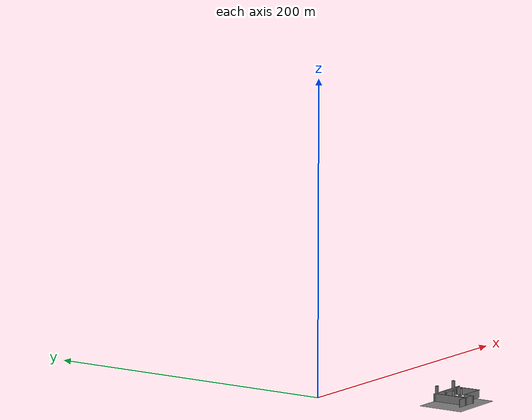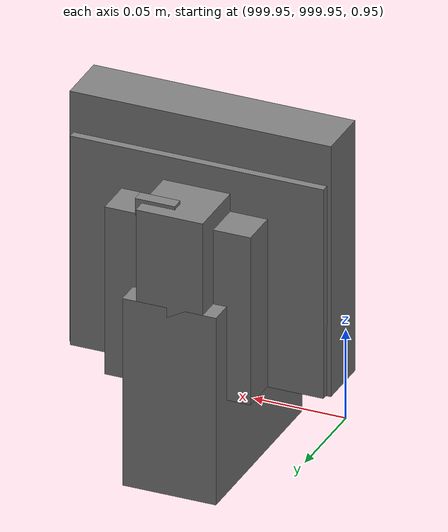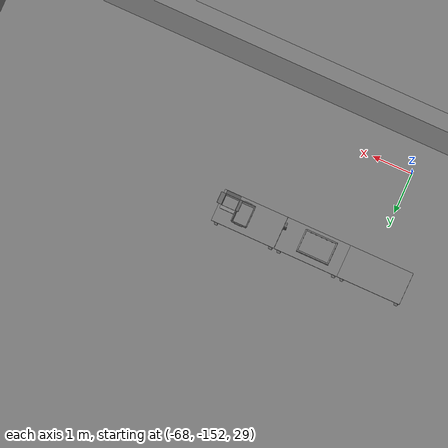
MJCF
<mujoco>
    <option gravity="0.000000000 0.000000000 -9.810000420" timestep="0.0049999999" integrator="implicitfast" density="1.225" viscosity="1.8000001e-05" noslip_iterations="10" iterations="100" sdf_iterations="50">
        <flag multiccd="disable"/>
    </option>
    <size memory="1000M"/>
    <compiler coordinate="local"/>
    <worldbody>
        <light cutoff="30" pos="0 1 1" dir="0 -1 -2"/>
        <light cutoff="30" pos="0 -1 1" dir="0 1 -2"/>
        <body pos="1000.000000000 1000.000000000 1.000000000" euler="0.000000000 0.000000000 180.000000000" name="openloong_gripper_2f85_fix_base_usda_battery_01">
            <geom contype="1" conaffinity="1" density="1000" type="box" material="" rgba="0.500000000 0.500000000 0.500000000 1.000000000" solimp="0.899999976 0.949999988 0.001000000" friction="1.000000000 0.005000000 0.000100000" solref="0.020000000 1.000000000" margin="0" condim="3" group="0" pos="-0.011123657 -0.041940309 0.101691343" quat="1.000000000 0.000000000 0.000000000 0.000000000" size="0.010800000 0.003375000 0.004725000" name="openloong_gripper_2f85_fix_base_usda_geom_5477D5CE_1B1F_4A91_86A8_2C9569B6ADA6"/>
            <geom contype="1" conaffinity="1" density="1000" type="box" material="" rgba="0.500000000 0.500000000 0.500000000 1.000000000" solimp="0.899999976 0.949999988 0.001000000" friction="1.000000000 0.005000000 0.000100000" solref="0.020000000 1.000000000" margin="0" condim="3" group="0" pos="-0.010876465 -0.044247437 0.047066893" quat="0.998702705 -0.050920475 0.000000000 0.000000000" size="0.009450001 0.002700000 0.024975000" name="openloong_gripper_2f85_fix_base_usda_geom_4977D7D5_DF46_49AE_AA86_0CAD2F7138C9"/>
            <geom contype="1" conaffinity="1" density="1000" type="box" material="" rgba="0.500000000 0.500000000 0.500000000 1.000000000" solimp="0.899999976 0.949999988 0.001000000" friction="1.000000000 0.005000000 0.000100000" solref="0.020000000 1.000000000" margin="0" condim="3" group="0" pos="-0.001235962 -0.000659180 0.047381196" quat="1.000000000 0.000000000 0.000000000 0.000000000" size="0.039420001 0.039150000 0.047250003" name="openloong_gripper_2f85_fix_base_usda_geom_A0CBD89B_AAFA_409C_B087_D77EF53DD0A4"/>
            <geom contype="1" conaffinity="1" density="1000" type="box" material="" rgba="0.500000000 0.500000000 0.500000000 1.000000000" solimp="0.899999976 0.949999988 0.001000000" friction="1.000000000 0.005000000 0.000100000" solref="0.020000000 1.000000000" margin="0" condim="3" group="0" pos="-0.010876465 -0.039138794 0.009851727" quat="1.000000000 0.000000000 0.000000000 0.000000000" size="0.009450001 0.010800000 0.013500000" name="openloong_gripper_2f85_fix_base_usda_geom_193A2866_A97F_483B_91DE_8A681E7FA678"/>
            <geom contype="1" conaffinity="1" density="1000" type="box" material="" rgba="0.500000000 0.500000000 0.500000000 1.000000000" solimp="0.899999976 0.949999988 0.001000000" friction="1.000000000 0.005000000 0.000100000" solref="0.020000000 1.000000000" margin="0" condim="3" group="0" pos="-0.010876465 -0.041528322 0.071508206" quat="1.000000000 0.000000000 0.000000000 0.000000000" size="0.009450001 0.002700000 0.027000001" name="openloong_gripper_2f85_fix_base_usda_geom_880736A2_2624_4C64_8265_14A84E6BF841"/>
            <freejoint name="openloong_gripper_2f85_fix_base_usda_battery_01_joint"/>
            <site size="0.005000000 0.005000000 0.005000000" rgba="0.500000000 0.500000000 0.500000000 1.000000000" pos="0.000000000 0.000000000 0.000000000" quat="0.999961913 0.008726500 0.000000000 0.000000000" group="0" type="sphere" name="openloong_gripper_2f85_fix_base_usda_battery_01site"/>
        </body>
        <body pos="1000.000000000 1000.000000000 1.000000000" euler="0.000000000 0.000000000 180.000000000" name="openloong_gripper_2f85_fix_base_usda_cpu_fan">
            <geom contype="1" conaffinity="1" density="1000" type="box" material="" rgba="0.500000000 0.500000000 0.500000000 1.000000000" solimp="0.899999976 0.949999988 0.001000000" friction="1.000000000 0.005000000 0.000100000" solref="0.020000000 1.000000000" margin="0" condim="3" group="0" pos="0.000000000 0.000000000 0.070034981" quat="0.000000000 0.000000000 0.000000000 1.000000000" size="0.070700005 0.014699999 0.070700005" name="openloong_gripper_2f85_fix_base_usda_geom_96BBE784_1693_4264_A9E3_9DAAACDA6D8D"/>
            <freejoint name="openloong_gripper_2f85_fix_base_usda_cpu_fan_joint"/>
            <site size="0.005000000 0.005000000 0.005000000" rgba="0.500000000 0.500000000 0.500000000 1.000000000" pos="0.000000000 0.000000000 0.000000000" quat="0.999961913 0.008726535 0.000000000 0.000000000" group="0" type="sphere" name="openloong_gripper_2f85_fix_base_usda_cpu_fancsite"/>
        </body>
        <body pos="1000.000000000 1000.000000000 1.000000000" euler="0.000011953 0.000005123 -179.999984741" name="openloong_gripper_2f85_fix_base_usda_intel_box">
            <geom contype="1" conaffinity="1" density="1000" type="box" material="" rgba="0.500000000 0.500000000 0.500000000 1.000000000" solimp="0.899999976 0.949999988 0.001000000" friction="1.000000000 0.005000000 0.000100000" solref="0.020000000 1.000000000" margin="0" condim="3" group="0" pos="0.000000000 -0.000067139 0.000082284" quat="0.707106709 0.000000225 0.000000253 0.707106650" size="0.052800003 0.025300000 0.052800003" name="openloong_gripper_2f85_fix_base_usda_geom_225BEC7C_CE14_4AF6_BB38_9B9CE4CB025B"/>
            <freejoint name="openloong_gripper_2f85_fix_base_usda_intel_box_joint"/>
            <site size="0.005000000 0.005000000 0.005000000" rgba="0.500000000 0.500000000 0.500000000 1.000000000" pos="0.000000000 0.000000000 0.000000000" quat="0.999961913 0.008726500 0.000000000 0.000000000" group="0" type="sphere" name="openloong_gripper_2f85_fix_base_usda_intel_boxsite"/>
        </body>
        <body pos="1000.000000000 1000.000000000 1.000000000" euler="0.000000000 0.000000000 180.000000000" name="openloong_gripper_2f85_fix_base_usda_wifi_box">
            <geom contype="1" conaffinity="1" density="1000" type="box" material="" rgba="0.500000000 0.500000000 0.500000000 1.000000000" solimp="0.899999976 0.949999988 0.001000000" friction="1.000000000 0.005000000 0.000100000" solref="0.020000000 1.000000000" margin="0" condim="3" group="0" pos="0.000000000 0.000000000 0.058978677" quat="0.000000000 0.000000047 0.000000000 1.000000000" size="0.068499997 0.018999999 0.059000000" name="openloong_gripper_2f85_fix_base_usda_geom_CE846646_2F37_4B48_B89F_EEF90555D6D4"/>
            <freejoint name="openloong_gripper_2f85_fix_base_usda_wifi_box_joint"/>
            <site size="0.005000000 0.005000000 0.005000000" rgba="0.500000000 0.500000000 0.500000000 1.000000000" pos="0.000000000 0.000000000 0.000000000" quat="0.999961913 0.008726500 0.000000000 0.000000000" group="0" type="sphere" name="openloong_gripper_2f85_fix_base_usda_wifi_boxsite"/>
        </body>
        <body pos="-65.865409851 -149.358810425 31.165992737" euler="-160.624938965 -88.633773804 75.616516113" mocap="true" name="spotlight5_SpotLight"/>
        <body pos="1000.000000000 999.999938965 1.000000000" euler="0.000000000 0.000000000 180.000000000" name="openloong_gripper_2f85_fix_base_usda_intelcore_i5">
            <geom contype="1" conaffinity="1" density="1000" type="box" material="" rgba="0.500000000 0.500000000 0.500000000 1.000000000" solimp="0.899999976 0.949999988 0.001000000" friction="1.000000000 0.005000000 0.000100000" solref="0.020000000 1.000000000" margin="0" condim="3" group="0" pos="0.000000000 0.000000000 0.051722717" quat="0.707106709 0.000000000 0.000000000 -0.707106769" size="0.052800000 0.018080002 0.052800000" name="openloong_gripper_2f85_fix_base_usda_geom_6A9322F3_9A02_4EFC_8FC7_EFD0E8E684EB"/>
            <freejoint name="openloong_gripper_2f85_fix_base_usda_intelcore_i5_joint"/>
            <site size="0.005000000 0.005000000 0.005000000" rgba="0.500000000 0.500000000 0.500000000 1.000000000" pos="0.000000000 0.000000000 0.000000000" quat="0.999961913 0.008726534 0.000000000 0.000000000" group="0" type="sphere" name="openloong_gripper_2f85_fix_base_usda_intelcore_i5site"/>
        </body>
        <body pos="-66.089195251 -149.012863159 31.168327332" euler="-177.146621704 65.584548950 7.955003738" mocap="true" name="spotlight2_SpotLight"/>
        <body pos="-65.895164490 -149.013336182 31.162212372" euler="-18.779434204 -29.240392685 177.037460327" mocap="true" name="spotlight1_SpotLight"/>
        <body pos="-64.866622925 -149.383972168 30.183746338" euler="89.999984741 89.999946594 0.000000000" name="openloong_gripper_2f85_fix_base_usda_bluebox_01">
            <geom contype="1" conaffinity="1" density="1000" type="box" material="" rgba="0.500000000 0.500000000 0.500000000 1.000000000" solimp="0.899999976 0.949999988 0.001000000" friction="1.000000000 0.005000000 0.000100000" solref="0.020000000 1.000000000" margin="0" condim="3" group="0" pos="0.276580811 0.187225342 0.000068665" quat="0.707106948 0.000077471 0.707106352 0.000077486" size="0.100000001 0.057999998 0.010000000" name="openloong_gripper_2f85_fix_base_usda_geom_6F78814A_72C0_40A6_922C_2859D502DB98"/>
            <geom contype="1" conaffinity="1" density="1000" type="box" material="" rgba="0.500000000 0.500000000 0.500000000 1.000000000" solimp="0.899999976 0.949999988 0.001000000" friction="1.000000000 0.005000000 0.000100000" solref="0.020000000 1.000000000" margin="0" condim="3" group="0" pos="0.000000000 0.002883911 0.000000000" quat="0.999999881 0.000000000 0.000000000 0.000000000" size="0.254000008 0.003000000 0.172000006" name="openloong_gripper_2f85_fix_base_usda_geom_9F5D302D_DD67_4BBD_B4E1_8291AFBAF3D0"/>
            <geom contype="1" conaffinity="1" density="1000" type="box" material="" rgba="0.500000000 0.500000000 0.500000000 1.000000000" solimp="0.899999976 0.949999988 0.001000000" friction="1.000000000 0.005000000 0.000100000" solref="0.020000000 1.000000000" margin="0" condim="3" group="0" pos="0.000000000 0.124874115 0.173484802" quat="0.999796331 0.020176515 -0.000000015 0.000000030" size="0.259999990 0.119999997 0.007000000" name="openloong_gripper_2f85_fix_base_usda_geom_BCB4E594_F61D_45D7_A364_1A74DC17CCA1"/>
            <geom contype="1" conaffinity="1" density="1000" type="box" material="" rgba="0.500000000 0.500000000 0.500000000 1.000000000" solimp="0.899999976 0.949999988 0.001000000" friction="1.000000000 0.005000000 0.000100000" solref="0.020000000 1.000000000" margin="0" condim="3" group="0" pos="0.000000000 0.124874115 -0.173469543" quat="0.999796331 -0.020176545 -0.000000015 0.000000000" size="0.259999990 0.119999997 0.007000000" name="openloong_gripper_2f85_fix_base_usda_geom_5C1B00DD_B01A_488D_802D_81EBE129178A"/>
            <geom contype="1" conaffinity="1" density="1000" type="box" material="" rgba="0.500000000 0.500000000 0.500000000 1.000000000" solimp="0.899999976 0.949999988 0.001000000" friction="1.000000000 0.005000000 0.000100000" solref="0.020000000 1.000000000" margin="0" condim="3" group="0" pos="0.000000000 0.214008331 0.188980103" quat="0.999912977 0.013176724 0.000000015 0.000000000" size="0.259999990 0.029999999 0.012500000" name="openloong_gripper_2f85_fix_base_usda_geom_2B4B202E_C097_4488_B3F2_8913527874A6"/>
            <geom contype="1" conaffinity="1" density="1000" type="box" material="" rgba="0.500000000 0.500000000 0.500000000 1.000000000" solimp="0.899999976 0.949999988 0.001000000" friction="1.000000000 0.005000000 0.000100000" solref="0.020000000 1.000000000" margin="0" condim="3" group="0" pos="-0.258361816 0.125289917 0.001876831" quat="0.702796936 -0.020792112 0.710783124 0.020769298" size="0.189999998 0.119999997 0.009000000" name="openloong_gripper_2f85_fix_base_usda_geom_7044CD03_55DA_42D7_8A96_2A2A209EB174"/>
            <geom contype="1" conaffinity="1" density="1000" type="box" material="" rgba="0.500000000 0.500000000 0.500000000 1.000000000" solimp="0.899999976 0.949999988 0.001000000" friction="1.000000000 0.005000000 0.000100000" solref="0.020000000 1.000000000" margin="0" condim="3" group="0" pos="0.000000000 0.214008331 -0.188980103" quat="0.999912977 -0.013176769 0.000000030 0.000000015" size="0.259999990 0.029999999 0.012500000" name="openloong_gripper_2f85_fix_base_usda_geom_209517C7_EE94_4310_A898_E50DC301230F"/>
            <geom contype="1" conaffinity="1" density="1000" type="box" material="" rgba="0.500000000 0.500000000 0.500000000 1.000000000" solimp="0.899999976 0.949999988 0.001000000" friction="1.000000000 0.005000000 0.000100000" solref="0.020000000 1.000000000" margin="0" condim="3" group="0" pos="-0.276611328 0.187225342 0.000068665" quat="0.707106650 0.000077441 0.707106709 0.000077456" size="0.100000001 0.057999998 0.010000000" name="openloong_gripper_2f85_fix_base_usda_geom_243579E6_F3AD_4A90_8E0C_7EB4B9A7422F"/>
            <geom contype="1" conaffinity="1" density="1000" type="box" material="" rgba="0.500000000 0.500000000 0.500000000 1.000000000" solimp="0.899999976 0.949999988 0.001000000" friction="1.000000000 0.005000000 0.000100000" solref="0.020000000 1.000000000" margin="0" condim="3" group="0" pos="0.258331299 0.125289917 0.001876831" quat="0.702851415 0.018856421 0.710823774 -0.019329369" size="0.189999998 0.119999997 0.009000000" name="openloong_gripper_2f85_fix_base_usda_geom_3CD2FEF5_F851_42E2_8C74_B241E7646F33"/>
            <freejoint name="openloong_gripper_2f85_fix_base_usda_bluebox_01_joint"/>
            <site size="0.005000000 0.005000000 0.005000000" rgba="0.500000000 0.500000000 0.500000000 1.000000000" pos="0.000000000 0.000000000 0.000000000" quat="0.999961913 0.008726534 0.000000000 0.000000000" group="0" type="sphere" name="openloong_gripper_2f85_fix_base_usda_bluebox_01site"/>
        </body>
        <body pos="-64.496299744 -149.491867065 30.235729218" euler="0.000000000 0.000000000 89.999946594" name="openloong_gripper_2f85_fix_base_usda_cardboardbox_01">
            <geom contype="1" conaffinity="1" density="1000" type="box" material="" rgba="0.500000000 0.500000000 0.500000000 1.000000000" solimp="0.899999976 0.949999988 0.001000000" friction="1.000000000 0.005000000 0.000100000" solref="0.020000000 1.000000000" margin="0" condim="3" group="0" pos="-0.003166199 -0.004086494 0.005052090" quat="1.000000000 0.000000000 0.000000000 0.000000000" size="0.142499998 0.177500010 0.005000000" name="openloong_gripper_2f85_fix_base_usda_geom_0BF08AAF_59BE_4930_AB95_9DD7A97A1AB9"/>
            <geom contype="1" conaffinity="1" density="1000" type="box" material="" rgba="0.500000000 0.500000000 0.500000000 1.000000000" solimp="0.899999976 0.949999988 0.001000000" friction="1.000000000 0.005000000 0.000100000" solref="0.020000000 1.000000000" margin="0" condim="3" group="0" pos="-0.003166199 0.170316696 0.150570869" quat="1.000000000 0.000000000 0.000000000 0.000000000" size="0.142499998 0.005000000 0.149999991" name="openloong_gripper_2f85_fix_base_usda_geom_87AD1FE4_F1BF_4109_A3D6_BE0D3F5C5AA9"/>
            <geom contype="1" conaffinity="1" density="1000" type="box" material="" rgba="0.500000000 0.500000000 0.500000000 1.000000000" solimp="0.899999976 0.949999988 0.001000000" friction="1.000000000 0.005000000 0.000100000" solref="0.020000000 1.000000000" margin="0" condim="3" group="0" pos="-0.147399902 -0.005307198 0.150570869" quat="1.000000000 0.000000000 0.000000000 0.000000000" size="0.005000000 0.177500010 0.149999991" name="openloong_gripper_2f85_fix_base_usda_geom_BCB4C26C_8036_4C8A_952A_93F88F8D7EAA"/>
            <geom contype="1" conaffinity="1" density="1000" type="box" material="" rgba="0.500000000 0.500000000 0.500000000 1.000000000" solimp="0.899999976 0.949999988 0.001000000" friction="1.000000000 0.005000000 0.000100000" solref="0.020000000 1.000000000" margin="0" condim="3" group="0" pos="0.140275955 -0.005307198 0.150570869" quat="1.000000000 0.000000000 0.000000000 0.000000000" size="0.005000000 0.177500010 0.149999991" name="openloong_gripper_2f85_fix_base_usda_geom_C91D8E2E_9A9B_470A_BCDB_E94528D31FB4"/>
            <geom contype="1" conaffinity="1" density="1000" type="box" material="" rgba="0.500000000 0.500000000 0.500000000 1.000000000" solimp="0.899999976 0.949999988 0.001000000" friction="1.000000000 0.005000000 0.000100000" solref="0.020000000 1.000000000" margin="0" condim="3" group="0" pos="-0.003166199 -0.181550980 0.150570869" quat="1.000000000 0.000000000 0.000000000 0.000000000" size="0.142499998 0.005000000 0.149999991" name="openloong_gripper_2f85_fix_base_usda_geom_5CD4D9C9_122A_4006_8586_E11F33CB6E50"/>
            <freejoint name="openloong_gripper_2f85_fix_base_usda_cardboardbox_01_joint"/>
            <site size="0.005000000 0.005000000 0.005000000" rgba="0.500000000 0.500000000 0.500000000 1.000000000" pos="0.000000000 0.000000000 0.000000000" quat="0.999961913 0.008726535 0.000000000 0.000000000" group="0" type="sphere" name="openloong_gripper_2f85_fix_base_usda_site_30392491_462F_4385_96F2_156A9EAFF02C"/>
            <body pos="0.139160156 -0.004048347 0.301930904" euler="-179.999954224 49.383502960 179.999954224" name="openloong_gripper_2f85_fix_base_usda_A1_006">
                <geom contype="1" conaffinity="1" density="1000" type="box" material="" rgba="0.500000000 0.500000000 0.500000000 1.000000000" solimp="0.899999976 0.949999988 0.001000000" friction="1.000000000 0.005000000 0.000100000" solref="0.020000000 1.000000000" margin="0" condim="3" group="0" pos="-0.071587563 0.000009537 0.001745224" quat="0.999999881 0.000000000 0.000000000 0.000000000" size="0.071249999 0.179999992 0.002500000" name="openloong_gripper_2f85_fix_base_usda_geom_02A6F163_6A0D_4DD2_9202_7E6056BB3821"/>
                <joint armature="0" stiffness="0.07" damping="0.0099999998" axis="0.000000 1.000000 0.000000" type="hinge" name="openloong_gripper_2f85_fix_base_usda_A1_006"/>
            </body>
            <body pos="-0.145902634 -0.004086494 0.301938057" euler="-180.000000000 -60.000011444 -180.000000000" name="openloong_gripper_2f85_fix_base_usda_A2_006">
                <geom contype="1" conaffinity="1" density="1000" type="box" material="" rgba="0.500000000 0.500000000 0.500000000 1.000000000" solimp="0.899999976 0.949999988 0.001000000" friction="1.000000000 0.005000000 0.000100000" solref="0.020000000 1.000000000" margin="0" condim="3" group="0" pos="0.071268082 0.000009537 0.002717972" quat="0.000002921 0.000000000 -0.000000030 0.999999881" size="0.071249999 0.179999992 0.002500000" name="openloong_gripper_2f85_fix_base_usda_geom_52205A24_BF59_4620_B17B_CE0CCEB61EB3"/>
                <joint armature="0" stiffness="0.07" damping="0.0099999998" axis="0.000000 1.000000 0.000000" type="hinge" name="openloong_gripper_2f85_fix_base_usda_A2_006"/>
            </body>
            <body pos="-0.003385544 0.175991058 0.301930904" euler="-125.858116150 -0.000004561 0.000002331" name="openloong_gripper_2f85_fix_base_usda_B2_006">
                <geom contype="1" conaffinity="1" density="1000" type="box" material="" rgba="0.500000000 0.500000000 0.500000000 1.000000000" solimp="0.899999976 0.949999988 0.001000000" friction="1.000000000 0.005000000 0.000100000" solref="0.020000000 1.000000000" margin="0" condim="3" group="0" pos="0.000009537 -0.070939064 -0.002470016" quat="0.999614120 0.027776197 -0.000000015 0.000000030" size="0.137500003 0.064999998 0.005000000" name="openloong_gripper_2f85_fix_base_usda_geom_3303F755_A1A7_4B24_BB3A_615099651C3C"/>
                <joint armature="0" stiffness="0.07" damping="0.0099999998" axis="1.000000 0.000000 0.000000" type="hinge" name="openloong_gripper_2f85_fix_base_usda_B2_006"/>
            </body>
            <body pos="-0.003385544 -0.184140205 0.301938057" euler="147.805557251 0.000000000 0.000000000" name="openloong_gripper_2f85_fix_base_usda_B1_006">
                <geom contype="1" conaffinity="1" density="1000" type="box" material="" rgba="0.500000000 0.500000000 0.500000000 1.000000000" solimp="0.899999976 0.949999988 0.001000000" friction="1.000000000 0.005000000 0.000100000" solref="0.020000000 1.000000000" margin="0" condim="3" group="0" pos="-0.000028610 0.070202351 -0.002703667" quat="0.999614179 -0.027776167 0.000000000 0.000000000" size="0.137500003 0.064999998 0.005000000" name="openloong_gripper_2f85_fix_base_usda_geom_F3FD2E26_71D5_4257_8F60_A715F94C281F"/>
                <joint armature="0" stiffness="0.07" damping="0.0099999998" axis="1.000000 0.000000 0.000000" type="hinge" name="openloong_gripper_2f85_fix_base_usda_B1_006"/>
            </body>
        </body>
        <body pos="-65.882858276 -149.481979370 30.229999542" euler="-64.487716675 0.000000000 0.000000000" name="openloong_gripper_2f85_fix_base_usda_Barcode">
            <geom contype="1" conaffinity="1" density="1000" type="box" material="" rgba="0.500000000 0.500000000 0.500000000 1.000000000" solimp="0.899999976 0.949999988 0.001000000" friction="1.000000000 0.005000000 0.000100000" solref="0.020000000 1.000000000" margin="0" condim="3" group="0" pos="0.000000000 0.013038635 0.001419067" quat="0.000000000 0.000000000 0.000000000 1.000000119" size="0.034000002 0.010000000 0.017999999" name="openloong_gripper_2f85_fix_base_usda_geom_B41BFC36_60C4_4FE3_9C8B_75BE199091C9"/>
            <geom contype="1" conaffinity="1" density="1000" type="box" material="" rgba="0.500000000 0.500000000 0.500000000 1.000000000" solimp="0.899999976 0.949999988 0.001000000" friction="1.000000000 0.005000000 0.000100000" solref="0.020000000 1.000000000" margin="0" condim="3" group="0" pos="0.000000000 -0.035301208 -0.007095337" quat="0.000000000 0.000000000 -0.043619365 0.999048233" size="0.028999999 0.010000000 0.020000000" name="openloong_gripper_2f85_fix_base_usda_geom_AF492148_807E_496D_AC99_8DB8230DE5F4"/>
            <geom contype="1" conaffinity="1" density="1000" type="box" material="" rgba="0.500000000 0.500000000 0.500000000 1.000000000" solimp="0.899999976 0.949999988 0.001000000" friction="1.000000000 0.005000000 0.000100000" solref="0.020000000 1.000000000" margin="0" condim="3" group="0" pos="0.000000000 -0.043411255 -0.011749268" quat="0.922262907 0.386563420 0.000000000 0.000000000" size="0.026000001 0.010000000 0.020000000" name="openloong_gripper_2f85_fix_base_usda_geom_840B8FD5_0B14_43F5_9891_A2897FF42CE1"/>
            <geom contype="1" conaffinity="1" density="1000" type="box" material="" rgba="0.500000000 0.500000000 0.500000000 1.000000000" solimp="0.899999976 0.949999988 0.001000000" friction="1.000000000 0.005000000 0.000100000" solref="0.020000000 1.000000000" margin="0" condim="3" group="0" pos="0.000000000 -0.016967773 -0.031860352" quat="0.000000000 0.000000000 0.000000000 1.000000119" size="0.008000000 0.010000000 0.013000000" name="openloong_gripper_2f85_fix_base_usda_geom_FDFFDDCA_ED18_4792_9FE4_CD3B90DED9EA"/>
            <geom contype="1" conaffinity="1" density="1000" type="box" material="" rgba="0.500000000 0.500000000 0.500000000 1.000000000" solimp="0.899999976 0.949999988 0.001000000" friction="1.000000000 0.005000000 0.000100000" solref="0.020000000 1.000000000" margin="0" condim="3" group="0" pos="0.000000000 -0.001869202 0.000312805" quat="0.953716993 0.300705761 0.000000000 0.000000000" size="0.032000002 0.010000000 0.018999999" name="openloong_gripper_2f85_fix_base_usda_geom_1D785A75_B43B_4B7B_A43D_C0A1805E1BA0"/>
            <geom contype="1" conaffinity="1" density="1000" type="box" material="" rgba="0.500000000 0.500000000 0.500000000 1.000000000" solimp="0.899999976 0.949999988 0.001000000" friction="1.000000000 0.005000000 0.000100000" solref="0.020000000 1.000000000" margin="0" condim="3" group="0" pos="0.000000000 -0.019531250 -0.003173828" quat="0.953716993 0.300705761 0.000000000 0.000000000" size="0.030999999 0.010000000 0.020000000" name="openloong_gripper_2f85_fix_base_usda_geom_040BA20B_4BEC_4730_A4F0_AF5DBB0F732F"/>
            <geom contype="1" conaffinity="1" density="1000" type="box" material="" rgba="0.500000000 0.500000000 0.500000000 1.000000000" solimp="0.899999976 0.949999988 0.001000000" friction="1.000000000 0.005000000 0.000100000" solref="0.020000000 1.000000000" margin="0" condim="3" group="0" pos="0.000000000 -0.035301208 -0.007095337" quat="0.953716993 0.300705761 0.000000000 0.000000000" size="0.028999999 0.010000000 0.020000000" name="openloong_gripper_2f85_fix_base_usda_geom_6F3AA1E3_74D4_475D_88F7_7007F0E40F88"/>
            <geom contype="1" conaffinity="1" density="1000" type="box" material="" rgba="0.500000000 0.500000000 0.500000000 1.000000000" solimp="0.899999976 0.949999988 0.001000000" friction="1.000000000 0.005000000 0.000100000" solref="0.020000000 1.000000000" margin="0" condim="3" group="0" pos="0.000000000 -0.042617798 -0.071121216" quat="0.000000000 0.000000000 0.000000000 1.000000119" size="0.013000000 0.021000000 0.059999999" name="openloong_gripper_2f85_fix_base_usda_geom_4CB62E64_87D8_48D9_A772_3F99ECF38995"/>
            <freejoint name="openloong_gripper_2f85_fix_base_usda_Barcode_joint"/>
            <site size="0.005000000 0.005000000 0.005000000" rgba="0.500000000 0.500000000 0.500000000 1.000000000" pos="0.000000000 0.000000000 0.000000000" quat="1.000000000 0.000000000 0.000000000 0.000000000" group="0" type="sphere" name="openloong_gripper_2f85_fix_base_usda_Barcode_site"/>
        </body>
        <body pos="-66.745018005 -149.392349243 30.184000015" euler="0.000000000 0.000000000 89.999946594" name="[22331186587896]_Basket_01">
            <geom contype="1" conaffinity="1" density="1000" type="box" material="" rgba="0.500000000 0.500000000 0.500000000 1.000000000" solimp="0.899999976 0.949999988 0.001000000" friction="1.000000000 0.005000000 0.000100000" solref="0.020000000 1.000000000" margin="0" condim="3" group="0" pos="-0.052425385 0.389207840 0.089787483" quat="0.707107008 0.000000000 0.000000000 0.707106411" size="0.014249999 0.014249999 0.059999999" name="[22331186587896]_geom_7D26E584_820B_4EE0_819D_AB1BE70D4074"/>
            <geom contype="1" conaffinity="1" density="1000" type="box" material="" rgba="0.500000000 0.500000000 0.500000000 1.000000000" solimp="0.899999976 0.949999988 0.001000000" friction="1.000000000 0.005000000 0.000100000" solref="0.020000000 1.000000000" margin="0" condim="3" group="0" pos="0.264015198 -0.133043289 0.089787483" quat="0.707107008 0.000000000 0.000000000 0.707106411" size="0.014249999 0.014249999 0.059999999" name="[22331186587896]_geom_F980F279_1660_485E_BD8C_3BCD9CAF2437"/>
            <geom contype="1" conaffinity="1" density="1000" type="box" material="" rgba="0.500000000 0.500000000 0.500000000 1.000000000" solimp="0.899999976 0.949999988 0.001000000" friction="1.000000000 0.005000000 0.000100000" solref="0.020000000 1.000000000" margin="0" condim="3" group="0" pos="-0.264015198 -0.265548706 0.089793205" quat="0.707107008 0.000000000 0.000000000 0.707106411" size="0.014249999 0.014249999 0.059999999" name="[22331186587896]_geom_CC1B02D0_628F_4BFA_B128_AA21ABDE1B27"/>
            <geom contype="1" conaffinity="1" density="1000" type="box" material="" rgba="0.500000000 0.500000000 0.500000000 1.000000000" solimp="0.899999976 0.949999988 0.001000000" friction="1.000000000 0.005000000 0.000100000" solref="0.020000000 1.000000000" margin="0" condim="3" group="0" pos="-0.160263062 -0.389322281 0.089793205" quat="0.707107008 0.000000000 0.000000000 0.707106411" size="0.014249999 0.014249999 0.059999999" name="[22331186587896]_geom_2D80DC01_3CA2_40E2_9062_E982290153CA"/>
            <geom contype="1" conaffinity="1" density="1000" type="box" material="" rgba="0.500000000 0.500000000 0.500000000 1.000000000" solimp="0.899999976 0.949999988 0.001000000" friction="1.000000000 0.005000000 0.000100000" solref="0.020000000 1.000000000" margin="0" condim="3" group="0" pos="0.162265778 -0.389322281 0.089787483" quat="0.707107008 0.000000000 0.000000000 0.707106411" size="0.014249999 0.014249999 0.059999999" name="[22331186587896]_geom_0BB3F6B4_15E7_4B46_A991_033891C2BACE"/>
            <geom contype="1" conaffinity="1" density="1000" type="box" material="" rgba="0.500000000 0.500000000 0.500000000 1.000000000" solimp="0.899999976 0.949999988 0.001000000" friction="1.000000000 0.005000000 0.000100000" solref="0.020000000 1.000000000" margin="0" condim="3" group="0" pos="0.264015198 0.389207840 0.089787483" quat="0.707107008 0.000000000 0.000000000 0.707106411" size="0.014249999 0.014249999 0.059999999" name="[22331186587896]_geom_F28B4FCE_7365_48F2_81CA_96190BDAF776"/>
            <geom contype="1" conaffinity="1" density="1000" type="box" material="" rgba="0.500000000 0.500000000 0.500000000 1.000000000" solimp="0.899999976 0.949999988 0.001000000" friction="1.000000000 0.005000000 0.000100000" solref="0.020000000 1.000000000" margin="0" condim="3" group="0" pos="-0.264015198 -0.133043289 0.089793205" quat="0.707107008 0.000000000 0.000000000 0.707106411" size="0.014249999 0.014249999 0.059999999" name="[22331186587896]_geom_FC62028A_E13D_44B8_B474_771363DD3026"/>
            <geom contype="1" conaffinity="1" density="1000" type="box" material="" rgba="0.500000000 0.500000000 0.500000000 1.000000000" solimp="0.899999976 0.949999988 0.001000000" friction="1.000000000 0.005000000 0.000100000" solref="0.020000000 1.000000000" margin="0" condim="3" group="0" pos="-0.264026642 0.269256592 0.089793205" quat="0.707107008 0.000000000 0.000000000 0.707106411" size="0.014249999 0.014249999 0.059999999" name="[22331186587896]_geom_64671CF7_2A8A_44AA_98EA_FA1FD270FBE4"/>
            <geom contype="1" conaffinity="1" density="1000" type="box" material="" rgba="0.500000000 0.500000000 0.500000000 1.000000000" solimp="0.899999976 0.949999988 0.001000000" friction="1.000000000 0.005000000 0.000100000" solref="0.020000000 1.000000000" margin="0" condim="3" group="0" pos="0.054462433 0.389207840 0.089787483" quat="0.707107008 0.000000000 0.000000000 0.707106411" size="0.014249999 0.014249999 0.059999999" name="[22331186587896]_geom_F4659A13_05D4_483B_B914_3B5C65D66767"/>
            <geom contype="1" conaffinity="1" density="1000" type="box" material="" rgba="0.500000000 0.500000000 0.500000000 1.000000000" solimp="0.899999976 0.949999988 0.001000000" friction="1.000000000 0.005000000 0.000100000" solref="0.020000000 1.000000000" margin="0" condim="3" group="0" pos="0.054462433 -0.389322281 0.089787483" quat="0.707107008 0.000000000 0.000000000 0.707106411" size="0.014249999 0.014249999 0.059999999" name="[22331186587896]_geom_F810B78E_3640_4B48_AD14_33CE1C7F627C"/>
            <geom contype="1" conaffinity="1" density="1000" type="box" material="" rgba="0.500000000 0.500000000 0.500000000 1.000000000" solimp="0.899999976 0.949999988 0.001000000" friction="1.000000000 0.005000000 0.000100000" solref="0.020000000 1.000000000" margin="0" condim="3" group="0" pos="0.264015198 0.269256592 0.089793205" quat="0.707107008 0.000000000 0.000000000 0.707106411" size="0.014249999 0.014249999 0.059999999" name="[22331186587896]_geom_7D2466B8_B985_4463_B701_B7DEBD7011BD"/>
            <geom contype="1" conaffinity="1" density="1000" type="box" material="" rgba="0.500000000 0.500000000 0.500000000 1.000000000" solimp="0.899999976 0.949999988 0.001000000" friction="1.000000000 0.005000000 0.000100000" solref="0.020000000 1.000000000" margin="0" condim="3" group="0" pos="0.264015198 -0.389322281 0.089787483" quat="0.707107008 0.000000000 0.000000000 0.707106411" size="0.014249999 0.014249999 0.059999999" name="[22331186587896]_geom_8A3F0C26_AB62_4198_BC43_AA74946AF813"/>
            <geom contype="1" conaffinity="1" density="1000" type="box" material="" rgba="0.500000000 0.500000000 0.500000000 1.000000000" solimp="0.899999976 0.949999988 0.001000000" friction="1.000000000 0.005000000 0.000100000" solref="0.020000000 1.000000000" margin="0" condim="3" group="0" pos="0.000000000 0.000000000 0.015998840" quat="0.707107008 0.000000000 0.000000000 0.707106411" size="0.403499991 0.279000014 0.015750000" name="[22331186587896]_geom_2DE0D51E_D9A2_4208_B2B4_4A675BEE4BEA"/>
            <geom contype="1" conaffinity="1" density="1000" type="box" material="" rgba="0.500000000 0.500000000 0.500000000 1.000000000" solimp="0.899999976 0.949999988 0.001000000" friction="1.000000000 0.005000000 0.000100000" solref="0.020000000 1.000000000" margin="0" condim="3" group="0" pos="0.000000000 -0.389476776 0.163619041" quat="0.707107008 0.000000000 0.000000000 0.707106411" size="0.015000000 0.277500004 0.015750000" name="[22331186587896]_geom_2FCAFDAD_23AF_41C6_B0D3_C6D33EBC9EC3"/>
            <geom contype="1" conaffinity="1" density="1000" type="box" material="" rgba="0.500000000 0.500000000 0.500000000 1.000000000" solimp="0.899999976 0.949999988 0.001000000" friction="1.000000000 0.005000000 0.000100000" solref="0.020000000 1.000000000" margin="0" condim="3" group="0" pos="0.162265778 0.389207840 0.089787483" quat="0.707107008 0.000000000 0.000000000 0.707106411" size="0.014249999 0.014249999 0.059999999" name="[22331186587896]_geom_71173A94_F143_47A3_8169_1C71FAD82E5C"/>
            <geom contype="1" conaffinity="1" density="1000" type="box" material="" rgba="0.500000000 0.500000000 0.500000000 1.000000000" solimp="0.899999976 0.949999988 0.001000000" friction="1.000000000 0.005000000 0.000100000" solref="0.020000000 1.000000000" margin="0" condim="3" group="0" pos="0.000000000 0.389471054 0.163619041" quat="0.707107008 0.000000000 0.000000000 0.707106411" size="0.015000000 0.277500004 0.015750000" name="[22331186587896]_geom_26E52F79_59A9_44A9_ADCD_6D21C2EF7D3E"/>
            <geom contype="1" conaffinity="1" density="1000" type="box" material="" rgba="0.500000000 0.500000000 0.500000000 1.000000000" solimp="0.899999976 0.949999988 0.001000000" friction="1.000000000 0.005000000 0.000100000" solref="0.020000000 1.000000000" margin="0" condim="3" group="0" pos="-0.263511658 0.000000000 0.163619041" quat="0.707107008 0.000000000 0.000000000 0.707106411" size="0.403499991 0.015000000 0.015750000" name="[22331186587896]_geom_D023954C_2343_4951_9651_5C9F57476164"/>
            <geom contype="1" conaffinity="1" density="1000" type="box" material="" rgba="0.500000000 0.500000000 0.500000000 1.000000000" solimp="0.899999976 0.949999988 0.001000000" friction="1.000000000 0.005000000 0.000100000" solref="0.020000000 1.000000000" margin="0" condim="3" group="0" pos="-0.264015198 0.141334534 0.089793205" quat="0.707107008 0.000000000 0.000000000 0.707106411" size="0.014249999 0.014249999 0.059999999" name="[22331186587896]_geom_E63D7160_753D_4BE7_96B1_F8D02A41104B"/>
            <geom contype="1" conaffinity="1" density="1000" type="box" material="" rgba="0.500000000 0.500000000 0.500000000 1.000000000" solimp="0.899999976 0.949999988 0.001000000" friction="1.000000000 0.005000000 0.000100000" solref="0.020000000 1.000000000" margin="0" condim="3" group="0" pos="0.264015198 -0.265548706 0.089787483" quat="0.707107008 0.000000000 0.000000000 0.707106411" size="0.014249999 0.014249999 0.059999999" name="[22331186587896]_geom_F090634B_5627_4990_B0BF_3C966F0F4250"/>
            <geom contype="1" conaffinity="1" density="1000" type="box" material="" rgba="0.500000000 0.500000000 0.500000000 1.000000000" solimp="0.899999976 0.949999988 0.001000000" friction="1.000000000 0.005000000 0.000100000" solref="0.020000000 1.000000000" margin="0" condim="3" group="0" pos="-0.160263062 0.389207840 0.089787483" quat="0.707107008 0.000000000 0.000000000 0.707106411" size="0.014249999 0.014249999 0.059999999" name="[22331186587896]_geom_08C026B4_4250_4C8D_A155_94E8AF718EAD"/>
            <geom contype="1" conaffinity="1" density="1000" type="box" material="" rgba="0.500000000 0.500000000 0.500000000 1.000000000" solimp="0.899999976 0.949999988 0.001000000" friction="1.000000000 0.005000000 0.000100000" solref="0.020000000 1.000000000" margin="0" condim="3" group="0" pos="-0.052425385 -0.389322281 0.089787483" quat="0.707107008 0.000000000 0.000000000 0.707106411" size="0.014249999 0.014249999 0.059999999" name="[22331186587896]_geom_482CEA5E_C922_48F8_9718_3EA335619E6E"/>
            <geom contype="1" conaffinity="1" density="1000" type="box" material="" rgba="0.500000000 0.500000000 0.500000000 1.000000000" solimp="0.899999976 0.949999988 0.001000000" friction="1.000000000 0.005000000 0.000100000" solref="0.020000000 1.000000000" margin="0" condim="3" group="0" pos="-0.264026642 -0.389322281 0.089793205" quat="0.707107008 0.000000000 0.000000000 0.707106411" size="0.014249999 0.014249999 0.059999999" name="[22331186587896]_geom_A5FD76E7_52BF_44F7_9C7D_62E514A587A1"/>
            <geom contype="1" conaffinity="1" density="1000" type="box" material="" rgba="0.500000000 0.500000000 0.500000000 1.000000000" solimp="0.899999976 0.949999988 0.001000000" friction="1.000000000 0.005000000 0.000100000" solref="0.020000000 1.000000000" margin="0" condim="3" group="0" pos="0.264015198 0.141334534 0.089787483" quat="0.707107008 0.000000000 0.000000000 0.707106411" size="0.014249999 0.014249999 0.059999999" name="[22331186587896]_geom_064194EC_E5BF_479E_95DD_1774656B3753"/>
            <geom contype="1" conaffinity="1" density="1000" type="box" material="" rgba="0.500000000 0.500000000 0.500000000 1.000000000" solimp="0.899999976 0.949999988 0.001000000" friction="1.000000000 0.005000000 0.000100000" solref="0.020000000 1.000000000" margin="0" condim="3" group="0" pos="-0.264015198 0.389207840 0.089793205" quat="0.707107008 0.000000000 0.000000000 0.707106411" size="0.014249999 0.014249999 0.059999999" name="[22331186587896]_geom_C4AAE6B7_7FFF_45F2_A804_0D3C69983E03"/>
            <geom contype="1" conaffinity="1" density="1000" type="box" material="" rgba="0.500000000 0.500000000 0.500000000 1.000000000" solimp="0.899999976 0.949999988 0.001000000" friction="1.000000000 0.005000000 0.000100000" solref="0.020000000 1.000000000" margin="0" condim="3" group="0" pos="0.264015198 0.004480362 0.089787483" quat="0.707107008 0.000000000 0.000000000 0.707106411" size="0.014249999 0.014249999 0.059999999" name="[22331186587896]_geom_31F88CF5_0A69_4952_8B95_724D2D5B799C"/>
            <geom contype="1" conaffinity="1" density="1000" type="box" material="" rgba="0.500000000 0.500000000 0.500000000 1.000000000" solimp="0.899999976 0.949999988 0.001000000" friction="1.000000000 0.005000000 0.000100000" solref="0.020000000 1.000000000" margin="0" condim="3" group="0" pos="0.263694763 -0.000011444 0.163619041" quat="0.707107008 0.000000000 0.000000000 0.707106411" size="0.403499991 0.015000000 0.015750000" name="[22331186587896]_geom_6132864E_FDA6_47BD_8DBA_CD0D2B93D8AE"/>
            <geom contype="1" conaffinity="1" density="1000" type="box" material="" rgba="0.500000000 0.500000000 0.500000000 1.000000000" solimp="0.899999976 0.949999988 0.001000000" friction="1.000000000 0.005000000 0.000100000" solref="0.020000000 1.000000000" margin="0" condim="3" group="0" pos="-0.264015198 0.004480362 0.089793205" quat="0.707107008 0.000000000 0.000000000 0.707106411" size="0.014249999 0.014249999 0.059999999" name="[22331186587896]_geom_F4505FE7_FAEC_4A45_AB8B_8A1F1D7A6747"/>
            <freejoint name="[22331186587896]_joint_E9A62F49_30AE_4E92_870A_3F06D1E642F6"/>
        </body>
        <body pos="0.000000000 0.000000000 0.000000000" euler="0.000000000 0.000000000 0.000000000" name="Static Objects_Static Objects">
            <geom contype="1" conaffinity="1" density="1000" type="box" material="" rgba="0.500000000 0.500000000 0.500000000 1.000000000" solimp="0.899999976 0.949999988 0.001000000" friction="1.000000000 0.005000000 0.000100000" solref="0.020000000 1.000000000" margin="0" condim="3" group="0" pos="-67.544113159 -149.365814209 29.727830887" quat="0.500000417 0.499999970 0.499999553 0.499999970" size="0.381000012 0.319999993 0.041000001" name="Static Objects_geom_DADC339F_885A_4992_945B_F1AB2856C16F"/>
            <geom contype="1" conaffinity="1" density="1000" type="box" material="" rgba="0.500000000 0.500000000 0.500000000 1.000000000" solimp="0.899999976 0.949999988 0.001000000" friction="1.000000000 0.005000000 0.000100000" solref="0.020000000 1.000000000" margin="0" condim="3" group="0" pos="-68.239501953 -149.365814209 30.086868286" quat="0.500000417 0.499999970 0.499999553 0.499999970" size="0.370999992 0.039500002 0.745000005" name="Static Objects_geom_4803841A_5CB2_41FD_A24E_F909D590609C"/>
            <geom contype="1" conaffinity="1" density="1000" type="box" material="" rgba="0.500000000 0.500000000 0.500000000 1.000000000" solimp="0.899999976 0.949999988 0.001000000" friction="1.000000000 0.005000000 0.000100000" solref="0.020000000 1.000000000" margin="0" condim="3" group="0" pos="-68.239501953 -149.365814209 30.147235870" quat="0.500000417 0.499999970 0.499999553 0.499999970" size="0.400000006 0.022000000 0.800000012" name="Static Objects_geom_D0E9B660_BD1D_40E6_9E6B_7D05B9484F6F"/>
            <geom contype="1" conaffinity="1" density="1000" type="box" material="" rgba="0.500000000 0.500000000 0.500000000 1.000000000" solimp="0.899999976 0.949999988 0.001000000" friction="1.000000000 0.005000000 0.000100000" solref="0.020000000 1.000000000" margin="0" condim="3" group="0" pos="-68.934890747 -149.365814209 29.727830887" quat="0.500000417 0.499999970 0.499999553 0.499999970" size="0.381000012 0.319999993 0.041000001" name="Static Objects_geom_405602E0_C03B_4CDC_A07A_2AE3F154EEB3"/>
            <geom contype="1" conaffinity="1" density="1000" type="box" material="" rgba="0.500000000 0.500000000 0.500000000 1.000000000" solimp="0.899999976 0.949999988 0.001000000" friction="1.000000000 0.005000000 0.000100000" solref="0.020000000 1.000000000" margin="0" condim="3" group="0" pos="-68.239501953 -149.365814209 29.561563492" quat="0.500000417 0.499999970 0.499999553 0.499999970" size="0.020000000 0.022000000 0.660000026" name="Static Objects_geom_0934D1FA_3099_4AF3_9B09_4C1069D7EAAB"/>
            <geom contype="1" conaffinity="1" density="1000" type="box" material="" rgba="0.500000000 0.500000000 0.500000000 1.000000000" solimp="0.899999976 0.949999988 0.001000000" friction="1.000000000 0.005000000 0.000100000" solref="0.020000000 1.000000000" margin="0" condim="3" group="0" pos="-65.945671082 -149.365814209 29.727830887" quat="0.500000417 0.499999970 0.499999553 0.499999970" size="0.381000012 0.319999993 0.041000001" name="Static Objects_geom_9B6CE4DC_A5E3_4B0F_A0FC_C5B43C1232D5"/>
            <geom contype="1" conaffinity="1" density="1000" type="box" material="" rgba="0.500000000 0.500000000 0.500000000 1.000000000" solimp="0.899999976 0.949999988 0.001000000" friction="1.000000000 0.005000000 0.000100000" solref="0.020000000 1.000000000" margin="0" condim="3" group="0" pos="-66.641059875 -149.365814209 30.086868286" quat="0.500000417 0.499999970 0.499999553 0.499999970" size="0.370999992 0.039500002 0.745000005" name="Static Objects_geom_B9D25DB3_012E_4AD7_A78A_22F9F3239070"/>
            <geom contype="1" conaffinity="1" density="1000" type="box" material="" rgba="0.500000000 0.500000000 0.500000000 1.000000000" solimp="0.899999976 0.949999988 0.001000000" friction="1.000000000 0.005000000 0.000100000" solref="0.020000000 1.000000000" margin="0" condim="3" group="0" pos="-66.641059875 -149.365814209 30.147235870" quat="0.500000417 0.499999970 0.499999553 0.499999970" size="0.400000006 0.022000000 0.800000012" name="Static Objects_geom_AF17698F_F66B_4497_A9B7_C9585532EF59"/>
            <geom contype="1" conaffinity="1" density="1000" type="box" material="" rgba="0.500000000 0.500000000 0.500000000 1.000000000" solimp="0.899999976 0.949999988 0.001000000" friction="1.000000000 0.005000000 0.000100000" solref="0.020000000 1.000000000" margin="0" condim="3" group="0" pos="-67.336448669 -149.365814209 29.727830887" quat="0.500000417 0.499999970 0.499999553 0.499999970" size="0.381000012 0.319999993 0.041000001" name="Static Objects_geom_59A0A972_ABFC_4ABD_A4EB_57F44A944393"/>
            <geom contype="1" conaffinity="1" density="1000" type="box" material="" rgba="0.500000000 0.500000000 0.500000000 1.000000000" solimp="0.899999976 0.949999988 0.001000000" friction="1.000000000 0.005000000 0.000100000" solref="0.020000000 1.000000000" margin="0" condim="3" group="0" pos="-66.641059875 -149.365814209 29.561563492" quat="0.500000417 0.499999970 0.499999553 0.499999970" size="0.020000000 0.022000000 0.660000026" name="Static Objects_geom_DC481636_0B15_48F7_B000_CEE508E65A6B"/>
            <geom contype="1" conaffinity="1" density="1000" type="box" material="" rgba="0.500000000 0.500000000 0.500000000 1.000000000" solimp="0.899999976 0.949999988 0.001000000" friction="1.000000000 0.005000000 0.000100000" solref="0.020000000 1.000000000" margin="0" condim="3" group="0" pos="-64.338577271 -149.365814209 29.727830887" quat="0.500000417 0.499999970 0.499999553 0.499999970" size="0.381000012 0.319999993 0.041000001" name="Static Objects_geom_871D641A_169A_40C5_8774_7545D12771A3"/>
            <geom contype="1" conaffinity="1" density="1000" type="box" material="" rgba="0.500000000 0.500000000 0.500000000 1.000000000" solimp="0.899999976 0.949999988 0.001000000" friction="1.000000000 0.005000000 0.000100000" solref="0.020000000 1.000000000" margin="0" condim="3" group="0" pos="-65.033966064 -149.365814209 30.086868286" quat="0.500000417 0.499999970 0.499999553 0.499999970" size="0.370999992 0.039500002 0.745000005" name="Static Objects_geom_F0974A46_E920_4F76_9218_B2E08C61BAF7"/>
            <geom contype="1" conaffinity="1" density="1000" type="box" material="" rgba="0.500000000 0.500000000 0.500000000 1.000000000" solimp="0.899999976 0.949999988 0.001000000" friction="1.000000000 0.005000000 0.000100000" solref="0.020000000 1.000000000" margin="0" condim="3" group="0" pos="-65.033966064 -149.365814209 30.147235870" quat="0.500000417 0.499999970 0.499999553 0.499999970" size="0.400000006 0.022000000 0.800000012" name="Static Objects_geom_6214BB18_9FF3_4DEA_B8B4_A802D32B673B"/>
            <geom contype="1" conaffinity="1" density="1000" type="box" material="" rgba="0.500000000 0.500000000 0.500000000 1.000000000" solimp="0.899999976 0.949999988 0.001000000" friction="1.000000000 0.005000000 0.000100000" solref="0.020000000 1.000000000" margin="0" condim="3" group="0" pos="-65.729354858 -149.365814209 29.727830887" quat="0.500000417 0.499999970 0.499999553 0.499999970" size="0.381000012 0.319999993 0.041000001" name="Static Objects_geom_915FA72F_A2D4_4F3A_9048_F010B77AD8A5"/>
            <geom contype="1" conaffinity="1" density="1000" type="box" material="" rgba="0.500000000 0.500000000 0.500000000 1.000000000" solimp="0.899999976 0.949999988 0.001000000" friction="1.000000000 0.005000000 0.000100000" solref="0.020000000 1.000000000" margin="0" condim="3" group="0" pos="-65.033966064 -149.365814209 29.561563492" quat="0.500000417 0.499999970 0.499999553 0.499999970" size="0.020000000 0.022000000 0.660000026" name="Static Objects_geom_5B309670_5FA3_42F9_94BE_9C27149C209D"/>
            <geom contype="1" conaffinity="1" density="1000" type="box" material="" rgba="0.500000000 0.500000000 0.500000000 1.000000000" solimp="0.899999976 0.949999988 0.001000000" friction="1.000000000 0.005000000 0.000100000" solref="0.020000000 1.000000000" margin="0" condim="3" group="0" pos="-61.754566193 -137.853729248 33.906845093" quat="0.707107067 0.000000000 0.000000000 0.707106471" size="0.759999990 0.759999990 4.500000000" name="Static Objects_geom_69EB11E3_68C3_480F_B3BF_6BDA4ED2FAD5"/>
            <geom contype="1" conaffinity="1" density="1000" type="box" material="" rgba="0.500000000 0.500000000 0.500000000 1.000000000" solimp="0.899999976 0.949999988 0.001000000" friction="1.000000000 0.005000000 0.000100000" solref="0.020000000 1.000000000" margin="0" condim="3" group="0" pos="-57.511135101 -144.927108765 31.707921982" quat="1.000000000 0.000000000 0.000000000 0.000000000" size="0.200000003 8.000000000 2.299999952" name="Static Objects_geom_6D4629F9_D62D_465D_BA65_E298098414B2"/>
            <geom contype="1" conaffinity="1" density="1000" type="box" material="" rgba="0.500000000 0.500000000 0.500000000 1.000000000" solimp="0.899999976 0.949999988 0.001000000" friction="1.000000000 0.005000000 0.000100000" solref="0.020000000 1.000000000" margin="0" condim="3" group="0" pos="-80.517646790 -157.574050903 31.688196182" quat="0.707107067 0.000000000 0.000000000 0.707106471" size="0.600000024 0.600000024 2.299999952" name="Static Objects_geom_368C0123_8904_4C80_99C1_C7FE359F1C8A"/>
            <geom contype="1" conaffinity="1" density="1000" type="box" material="" rgba="0.500000000 0.500000000 0.500000000 1.000000000" solimp="0.899999976 0.949999988 0.001000000" friction="1.000000000 0.005000000 0.000100000" solref="0.020000000 1.000000000" margin="0" condim="3" group="0" pos="-80.711044312 -147.414932251 31.666158676" quat="1.000000000 0.000000000 0.000000000 0.000000000" size="0.200000003 10.000000000 2.299999952" name="Static Objects_geom_9E4D45D8_37B6_4235_9FDC_01AF86D0068A"/>
            <geom contype="1" conaffinity="1" density="1000" type="box" material="" rgba="0.500000000 0.500000000 0.500000000 1.000000000" solimp="0.899999976 0.949999988 0.001000000" friction="1.000000000 0.005000000 0.000100000" solref="0.020000000 1.000000000" margin="0" condim="3" group="0" pos="-57.687217712 -137.434692383 31.688196182" quat="0.707107067 0.000000000 0.000000000 0.707106471" size="0.600000024 0.600000024 2.299999952" name="Static Objects_geom_8DC4F267_8370_4CCB_B869_FD2968C45E03"/>
            <geom contype="1" conaffinity="1" density="1000" type="box" material="" rgba="0.500000000 0.500000000 0.500000000 1.000000000" solimp="0.899999976 0.949999988 0.001000000" friction="1.000000000 0.005000000 0.000100000" solref="0.020000000 1.000000000" margin="0" condim="3" group="0" pos="-69.537033081 -140.263229370 31.714921951" quat="0.707107067 0.000000000 0.000000000 0.707106471" size="0.759999990 4.500000000 2.299999952" name="Static Objects_geom_8DCEB76A_9129_45CB_9A20_6EC76B1DDC8F"/>
            <geom contype="1" conaffinity="1" density="1000" type="box" material="" rgba="0.500000000 0.500000000 0.500000000 1.000000000" solimp="0.899999976 0.949999988 0.001000000" friction="1.000000000 0.005000000 0.000100000" solref="0.020000000 1.000000000" margin="0" condim="3" group="0" pos="-80.073638916 -137.853713989 33.906845093" quat="0.707107067 0.000000000 0.000000000 0.707106471" size="0.759999990 0.759999990 4.500000000" name="Static Objects_geom_B889F819_71E5_481A_931E_8DFDAAFBF456"/>
            <geom contype="1" conaffinity="1" density="1000" type="box" material="" rgba="0.500000000 0.500000000 0.500000000 1.000000000" solimp="0.899999976 0.949999988 0.001000000" friction="1.000000000 0.005000000 0.000100000" solref="0.020000000 1.000000000" margin="0" condim="3" group="0" pos="-73.406707764 -155.734664917 31.707921982" quat="1.000000000 0.000000000 0.000000000 0.000000000" size="0.200000003 3.000000000 2.299999952" name="Static Objects_geom_DFA9948C_AC5A_40C2_AE87_148552B50ED3"/>
            <geom contype="1" conaffinity="1" density="1000" type="box" material="" rgba="0.500000000 0.500000000 0.500000000 1.000000000" solimp="0.899999976 0.949999988 0.001000000" friction="1.000000000 0.005000000 0.000100000" solref="0.020000000 1.000000000" margin="0" condim="3" group="0" pos="-68.497543335 -137.448257446 31.707921982" quat="0.707107067 0.000000000 0.000000000 0.707106471" size="0.200000003 14.000000000 2.299999952" name="Static Objects_geom_193E9FF7_360B_4131_95E4_7A1239656DD5"/>
            <geom contype="1" conaffinity="1" density="1000" type="cylinder" material="" rgba="0.500000000 0.500000000 0.500000000 1.000000000" solimp="0.899999976 0.949999988 0.001000000" friction="1.000000000 0.005000000 0.000100000" solref="0.020000000 1.000000000" margin="0" condim="3" group="0" pos="-68.868522644 -142.134506226 31.711090088" quat="0.707107067 0.000000000 0.000000000 0.707106471" size="0.509999990 2.299999952 1.000000000" name="Static Objects_geom_DD60822F_9AB1_4E49_BB4A_80EAE4106DC4"/>
            <geom contype="1" conaffinity="1" density="1000" type="plane" material="" rgba="0.500000000 0.500000000 0.500000000 1.000000000" solimp="0.899999976 0.949999988 0.001000000" friction="1.000000000 0.005000000 0.000100000" solref="0.020000000 1.000000000" margin="0" condim="3" group="0" pos="-72.873703003 -147.131927490 29.409669876" quat="1.000000000 0.000000000 0.000000000 0.000000000" size="18.000000000 14.000000000 1.000000000" name="Static Objects_geom_A450ED42_F111_4E82_8880_E98C2537D0C8"/>
            <geom contype="1" conaffinity="1" density="1000" type="box" material="" rgba="0.500000000 0.500000000 0.500000000 1.000000000" solimp="0.899999976 0.949999988 0.001000000" friction="1.000000000 0.005000000 0.000100000" solref="0.020000000 1.000000000" margin="0" condim="3" group="0" pos="-79.943580627 -157.782272339 31.707921982" quat="0.707107067 0.000000000 0.000000000 0.707106471" size="0.200000003 7.000000000 2.299999952" name="Static Objects_geom_7AA64F14_2578_4315_A1BC_FFFA7A318944"/>
            <geom contype="1" conaffinity="1" density="1000" type="box" material="" rgba="0.500000000 0.500000000 0.500000000 1.000000000" solimp="0.899999976 0.949999988 0.001000000" friction="1.000000000 0.005000000 0.000100000" solref="0.020000000 1.000000000" margin="0" condim="3" group="0" pos="-65.421028137 -152.903442383 31.707921982" quat="0.707107067 0.000000000 0.000000000 0.707106471" size="0.200000003 7.800000191 2.299999952" name="Static Objects_geom_7CB3CC85_CF75_4B2C_8C67_D734648490E8"/>
            <geom contype="1" conaffinity="1" density="1000" type="box" material="" rgba="0.500000000 0.500000000 0.500000000 1.000000000" solimp="0.899999976 0.949999988 0.001000000" friction="1.000000000 0.005000000 0.000100000" solref="0.020000000 1.000000000" margin="0" condim="3" group="0" pos="-74.776908875 -149.964416504 31.688196182" quat="1.000000000 0.000000000 0.000000000 0.000000000" size="0.600000024 0.409999996 2.299999952" name="Static Objects_geom_F6E62A36_05B8_4B3F_8363_F7BE40150FB1"/>
            <geom contype="1" conaffinity="1" density="1000" type="cylinder" material="" rgba="0.500000000 0.500000000 0.500000000 1.000000000" solimp="0.899999976 0.949999988 0.001000000" friction="1.000000000 0.005000000 0.000100000" solref="0.020000000 1.000000000" margin="0" condim="3" group="0" pos="-60.161884308 -142.134506226 31.711090088" quat="0.707107067 0.000000000 0.000000000 0.707106471" size="0.509999990 2.299999952 1.000000000" name="Static Objects_geom_1790DA38_E076_4B69_BCE9_4A1A9A660F61"/>
            <geom contype="1" conaffinity="1" density="1000" type="cylinder" material="" rgba="0.500000000 0.500000000 0.500000000 1.000000000" solimp="0.899999976 0.949999988 0.001000000" friction="1.000000000 0.005000000 0.000100000" solref="0.020000000 1.000000000" margin="0" condim="3" group="0" pos="-75.382453918 -149.963455200 31.711090088" quat="0.707107067 0.000000000 0.000000000 0.707106471" size="0.409999996 2.299999952 1.000000000" name="Static Objects_geom_A3DC3F80_7A72_4599_A323_39F251620DBB"/>
            <geom contype="1" conaffinity="1" density="1000" type="cylinder" material="" rgba="0.500000000 0.500000000 0.500000000 1.000000000" solimp="0.899999976 0.949999988 0.001000000" friction="1.000000000 0.005000000 0.000100000" solref="0.020000000 1.000000000" margin="0" condim="3" group="0" pos="-74.154960632 -149.963455200 31.711090088" quat="0.707107067 0.000000000 0.000000000 0.707106471" size="0.409999996 2.299999952 1.000000000" name="Static Objects_geom_B3A270C1_6C3B_4E1B_964E_5604283AC91A"/>
            <geom contype="1" conaffinity="1" density="1000" type="cylinder" material="" rgba="0.500000000 0.500000000 0.500000000 1.000000000" solimp="0.899999976 0.949999988 0.001000000" friction="1.000000000 0.005000000 0.000100000" solref="0.020000000 1.000000000" margin="0" condim="3" group="0" pos="-77.566612244 -142.134506226 31.711090088" quat="0.707107067 0.000000000 0.000000000 0.707106471" size="0.509999990 2.299999952 1.000000000" name="Static Objects_geom_E7BFB5F7_ABDA_4A73_8D6E_6E3777A85102"/>
        </body>
        <body pos="-66.291030884 -149.869689941 29.018842697" euler="0.000000000 0.000000000 89.999946594" mocap="true" name="openloong_gripper_2f85_fix_base_usda_leftHandMocap"/>
        <body pos="-66.291030884 -149.869689941 29.018842697" euler="0.000000000 0.000000000 89.999946594" mocap="true" name="openloong_gripper_2f85_fix_base_usda_rightHandMocap"/>
        <body pos="-66.291030884 -149.869689941 30.218843460" euler="0.000000000 0.000000000 89.999946594" name="openloong_gripper_2f85_fix_base_usda_base_link">
            <geom contype="1" conaffinity="1" density="1000" type="mesh" material="" rgba="0.783999979 0.783999979 0.783999979 1.000000000" solimp="0.899999976 0.949999988 0.001000000" friction="1.000000000 0.005000000 0.000100000" solref="0.020000000 1.000000000" margin="0" condim="3" group="3" mesh="base_link" pos="0.000000000 0.000000000 0.000000000" quat="1.000000000 0.000000000 0.000000000 0.000000000" size="1.000000000 1.000000000 1.000000000" name="openloong_gripper_2f85_fix_base_usda__geom_7_10E13A70_88CA_4D74_AE07_C46DC3447519"/>
            <site size="0.005000000 0.005000000 0.005000000" rgba="0.500000000 0.500000000 0.500000000 1.000000000" pos="0.000000000 0.000000000 0.000000000" quat="1.000000000 0.000000000 0.000000000 0.000000000" group="0" type="sphere" name="openloong_gripper_2f85_fix_base_usda_imu"/>
            <inertial mass="22.447001" pos="-0.005664100 -0.001336700 0.238289997" diaginertia="0.374352545 0.277180195 0.220617250" quat="0.999247074 0.035235517 -0.015086859 0.006023135"/>
            <body pos="0.000000000 0.000000000 0.299997330" euler="0.000000000 0.000000000 0.000000000" name="openloong_gripper_2f85_fix_base_usda_dummy_body">
                <geom contype="1" conaffinity="1" density="1000" type="sphere" material="" rgba="0.783999979 0.783999979 0.783999979 1.000000000" solimp="0.899999976 0.949999988 0.001000000" friction="1.000000000 0.005000000 0.000100000" solref="0.020000000 1.000000000" margin="0" condim="3" group="3" pos="0.000000000 0.000000000 0.000000000" quat="1.000000000 0.000000000 0.000000000 0.000000000" size="0.010000000 0.000000000 0.000000000" name="openloong_gripper_2f85_fix_base_usda__geom_8_29B51503_8C8F_4EDF_AA5D_8B48849F2314"/>
                <joint armature="0.0099999998" stiffness="0" damping="0.1" axis="0.000000 0.000000 1.000000" type="hinge" name="openloong_gripper_2f85_fix_base_usda_dummy_joint"/>
                <site size="0.010000000 0.005000000 0.005000000" rgba="0.500000000 0.500000000 0.500000000 1.000000000" pos="0.000000000 0.000000000 0.000000000" quat="1.000000000 0.000000000 0.000000000 0.000000000" group="3" type="sphere" name="openloong_gripper_2f85_fix_base_usda_dummy_site"/>
            </body>
            <body pos="0.009002686 0.000000000 0.406400681" euler="0.000000000 0.000000000 0.000000000" name="openloong_gripper_2f85_fix_base_usda_Link_head_yaw">
                <geom contype="1" conaffinity="1" density="1000" type="mesh" material="" rgba="0.783999979 0.783999979 0.783999979 1.000000000" solimp="0.899999976 0.949999988 0.001000000" friction="1.000000000 0.005000000 0.000100000" solref="0.020000000 1.000000000" margin="0" condim="3" group="3" mesh="Link_head_yaw" pos="0.000000000 0.000000000 0.000000000" quat="1.000000000 0.000000000 0.000000000 0.000000000" size="1.000000000 1.000000000 1.000000000" name="openloong_gripper_2f85_fix_base_usda__geom_10_CF9B9F76_E7B5_41DA_934E_197DD28B5A7E"/>
                <inertial mass="0.84249002" pos="0.000000000 -0.002081400 0.044801001" diaginertia="0.000700588 0.000629000 0.000553812" quat="0.706933022 -0.015675601 0.015677100 0.706933022"/>
                <body pos="0.000000000 -0.034599304 0.048500061" euler="0.000000000 0.000000000 0.000000000" name="openloong_gripper_2f85_fix_base_usda_Link_head_pitch">
                    <geom contype="1" conaffinity="1" density="1000" type="mesh" material="" rgba="0.783999979 0.783999979 0.783999979 1.000000000" solimp="0.899999976 0.949999988 0.001000000" friction="1.000000000 0.005000000 0.000100000" solref="0.020000000 1.000000000" margin="0" condim="3" group="3" mesh="Link_head_pitch" pos="0.000000000 0.000000000 0.000000000" quat="1.000000000 0.000000000 0.000000000 0.000000000" size="1.000000000 1.000000000 1.000000000" name="openloong_gripper_2f85_fix_base_usda__geom_12_FA51279E_8A6D_4EF4_A8C2_335B4EEC162A"/>
                    <inertial mass="1.3943" pos="0.020569000 0.033004001 0.125000000" diaginertia="0.006381400 0.006289940 0.004481460" quat="0.973390222 0.008406822 0.228157058 0.019624906"/>
                    <body pos="0.000000000 0.029998779 0.000000000" euler="0.000000000 0.000000000 0.000000000" name="openloong_gripper_2f85_fix_base_usda_neck_center_body">
                        <site size="0.010000000 0.005000000 0.005000000" rgba="0.500000000 0.500000000 0.500000000 1.000000000" pos="0.000000000 0.000000000 0.000000000" quat="1.000000000 0.000000000 0.000000000 0.000000000" group="3" type="sphere" name="openloong_gripper_2f85_fix_base_usda_neck_center_site"/>
                        <body pos="0.020004272 0.000000000 0.149999619" euler="-0.000002229 39.998176575 -90.000205994" name="openloong_gripper_2f85_fix_base_usda_camera_head">
                            <site size="0.010000000 0.005000000 0.005000000" rgba="0.500000000 0.500000000 0.500000000 1.000000000" pos="0.000000000 0.000000000 0.000000000" quat="1.000000000 0.000000000 0.000000000 0.000000000" group="3" type="sphere" name="openloong_gripper_2f85_fix_base_usda_camera_head_site"/>
                        </body>
                    </body>
                </body>
            </body>
            <body pos="0.003997803 -0.161598206 0.392200470" euler="0.000000000 0.000000000 0.000000000" name="openloong_gripper_2f85_fix_base_usda_Link_arm_r_01">
                <geom contype="1" conaffinity="1" density="1000" type="mesh" material="" rgba="0.783999979 0.783999979 0.783999979 1.000000000" solimp="0.899999976 0.949999988 0.001000000" friction="1.000000000 0.005000000 0.000100000" solref="0.020000000 1.000000000" margin="0" condim="3" group="3" mesh="Link_arm_r_01" pos="0.000000000 0.000000000 0.000000000" quat="1.000000000 0.000000000 0.000000000 0.000000000" size="1.000000000 1.000000000 1.000000000" name="openloong_gripper_2f85_fix_base_usda__geom_14_3DF4E6FC_BD0C_4D1E_AB2D_DA87E117CC78"/>
                <joint armature="0.0099999998" stiffness="0" damping="1" axis="0.000000 -1.000000 0.000000" limited="true" range="-170.000015259 170.000015259" type="hinge" name="openloong_gripper_2f85_fix_base_usda_J_arm_r_01"/>
                <inertial mass="0.75641" pos="0.004494600 -0.038293999 -0.000001874" diaginertia="0.000842990 0.000803050 0.000587120" quat="-0.000163502 0.707098067 0.000812463 0.707115054"/>
                <body pos="-0.041992188 -0.041000366 0.000000000" euler="0.000000000 0.000000000 0.000000000" name="openloong_gripper_2f85_fix_base_usda_Link_arm_r_02">
                    <geom contype="1" conaffinity="1" density="1000" type="mesh" material="" rgba="0.783999979 0.783999979 0.783999979 1.000000000" solimp="0.899999976 0.949999988 0.001000000" friction="1.000000000 0.005000000 0.000100000" solref="0.020000000 1.000000000" margin="0" condim="3" group="3" mesh="Link_arm_r_02" pos="0.000000000 0.000000000 0.000000000" quat="1.000000000 0.000000000 0.000000000 0.000000000" size="1.000000000 1.000000000 1.000000000" name="openloong_gripper_2f85_fix_base_usda__geom_16_A9DA0BC1_95E0_411C_A3E7_0011AF549C26"/>
                    <joint armature="0.0099999998" stiffness="0" damping="1" axis="-1.000000 0.000000 0.000000" limited="true" range="-105.000244141 105.000244141" type="hinge" name="openloong_gripper_2f85_fix_base_usda_J_arm_r_02"/>
                    <inertial mass="0.98500001" pos="0.041999999 -0.067430697 0.000000000" diaginertia="0.002262690 0.001730990 0.001154020" quat="0.500000000 0.500000000 -0.500000000 0.500000000"/>
                    <body pos="0.041992188 -0.122596741 0.000000000" euler="0.000000000 0.000000000 0.000000000" name="openloong_gripper_2f85_fix_base_usda_Link_arm_r_03">
                        <geom contype="1" conaffinity="1" density="1000" type="mesh" material="" rgba="0.783999979 0.783999979 0.783999979 1.000000000" solimp="0.899999976 0.949999988 0.001000000" friction="1.000000000 0.005000000 0.000100000" solref="0.020000000 1.000000000" margin="0" condim="3" group="3" mesh="Link_arm_r_03" pos="0.000000000 0.000000000 0.000000000" quat="1.000000000 0.000000000 0.000000000 0.000000000" size="1.000000000 1.000000000 1.000000000" name="openloong_gripper_2f85_fix_base_usda__geom_18_896D672E_4226_46B6_9076_655FF2DD783A"/>
                        <joint armature="0.0099999998" stiffness="0" damping="1" axis="0.000000 -1.000000 0.000000" limited="true" range="-170.000015259 170.000015259" type="hinge" name="openloong_gripper_2f85_fix_base_usda_J_arm_r_03"/>
                        <inertial mass="0.95899999" pos="-0.001413580 -0.164663002 0.020757901" diaginertia="0.002101340 0.002064590 0.000754802" quat="0.560480952 0.454391927 -0.443732947 0.531497955"/>
                        <body pos="0.035293579 -0.177406311 0.023998260" euler="0.000000000 0.000000000 0.000000000" name="openloong_gripper_2f85_fix_base_usda_Link_arm_r_04">
                            <geom contype="1" conaffinity="1" density="1000" type="mesh" material="" rgba="0.783999979 0.783999979 0.783999979 1.000000000" solimp="0.899999976 0.949999988 0.001000000" friction="1.000000000 0.005000000 0.000100000" solref="0.020000000 1.000000000" margin="0" condim="3" group="3" mesh="Link_arm_r_04" pos="0.000000000 0.000000000 0.000000000" quat="1.000000000 0.000000000 0.000000000 0.000000000" size="1.000000000 1.000000000 1.000000000" name="openloong_gripper_2f85_fix_base_usda__geom_20_30F50805_E245_4B60_A8B1_7486E0442535"/>
                            <joint armature="0.0099999998" stiffness="0" damping="1" axis="-1.000000 0.000000 0.000000" limited="true" range="0.000000000 170.000015259" type="hinge" name="openloong_gripper_2f85_fix_base_usda_J_arm_r_04"/>
                            <inertial mass="0.60000002" pos="-0.038727000 -0.060766999 -0.021003000" diaginertia="0.001092610 0.000712422 0.000645102" quat="0.327701002 0.632602990 -0.467366993 0.523443997"/>
                            <body pos="-0.035293579 -0.103492737 -0.023998260" euler="0.000000000 0.000000000 0.000000000" name="openloong_gripper_2f85_fix_base_usda_Link_arm_r_05">
                                <geom contype="1" conaffinity="1" density="1000" type="mesh" material="" rgba="0.783999979 0.783999979 0.783999979 1.000000000" solimp="0.899999976 0.949999988 0.001000000" friction="1.000000000 0.005000000 0.000100000" solref="0.020000000 1.000000000" margin="0" condim="3" group="3" mesh="Link_arm_r_05" pos="0.000000000 0.000000000 0.000000000" quat="1.000000000 0.000000000 0.000000000 0.000000000" size="1.000000000 1.000000000 1.000000000" name="openloong_gripper_2f85_fix_base_usda__geom_22_0B90FF04_B720_481C_8FC7_2B1826F5874F"/>
                                <joint armature="0.0099999998" stiffness="0" damping="1" axis="0.000000 -1.000000 0.000000" limited="true" range="-170.000015259 170.000015259" type="hinge" name="openloong_gripper_2f85_fix_base_usda_J_arm_r_05"/>
                                <inertial mass="0.68976003" pos="0.000032712 -0.068658002 -0.000111780" diaginertia="0.002522510 0.002411100 0.000448695" quat="0.707660973 0.706543028 -0.002603360 0.002470550"/>
                                <body pos="-0.026489258 -0.196502686 0.000000000" euler="0.000000000 0.000000000 0.000000000" name="openloong_gripper_2f85_fix_base_usda_Link_arm_r_06">
                                    <geom contype="1" conaffinity="1" density="1000" type="mesh" material="" rgba="0.783999979 0.783999979 0.783999979 1.000000000" solimp="0.899999976 0.949999988 0.001000000" friction="1.000000000 0.005000000 0.000100000" solref="0.020000000 1.000000000" margin="0" condim="3" group="3" mesh="Link_arm_r_06" pos="0.000000000 0.000000000 0.000000000" quat="1.000000000 0.000000000 0.000000000 0.000000000" size="1.000000000 1.000000000 1.000000000" name="openloong_gripper_2f85_fix_base_usda__geom_24_F28E6B10_EA70_4F66_B59C_B4B1C5DE4DEF"/>
                                    <joint armature="0.0099999998" stiffness="0" damping="1" axis="1.000000 0.000000 0.000000" limited="true" range="-105.000244141 105.000244141" type="hinge" name="openloong_gripper_2f85_fix_base_usda_J_arm_r_06"/>
                                    <inertial mass="0.28" pos="0.026078001 -0.000000896 0.001663700" diaginertia="0.000156930 0.000145601 0.000104979" quat="0.707080841 0.001851080 0.001883810 0.707127810"/>
                                    <body pos="0.026489258 0.000000000 0.031799316" euler="0.000000000 0.000000000 0.000000000" name="openloong_gripper_2f85_fix_base_usda_Link_arm_r_07">
                                        <geom contype="1" conaffinity="1" density="1000" type="mesh" material="" rgba="0.783999979 0.783999979 0.783999979 1.000000000" solimp="0.899999976 0.949999988 0.001000000" friction="1.000000000 0.005000000 0.000100000" solref="0.020000000 1.000000000" margin="0" condim="3" group="3" mesh="Link_arm_r_07" pos="0.000000000 0.000000000 0.000000000" quat="1.000000000 0.000000000 0.000000000 0.000000000" size="1.000000000 1.000000000 1.000000000" name="openloong_gripper_2f85_fix_base_usda__geom_26_B4983E10_C8D8_4D36_BD91_FB967FB5CD0F"/>
                                        <joint armature="0.0099999998" stiffness="0" damping="1" axis="0.000000 0.000000 1.000000" limited="true" range="-60.000133514 60.000133514" type="hinge" name="openloong_gripper_2f85_fix_base_usda_J_arm_r_07"/>
                                        <inertial mass="0.61353999" pos="-0.007859000 -0.158170000 -0.027736001" diaginertia="0.003037610 0.002570910 0.000729379" quat="0.427542925 0.443532884 -0.553093910 0.560867906"/>
                                        <body pos="0.000000000 0.286994934 -0.270000458" euler="150.000350952 -0.000001649 -0.000000442" name="openloong_gripper_2f85_fix_base_usda_camera_wrist_r">
                                            <site size="0.010000000 0.005000000 0.005000000" rgba="0.500000000 0.500000000 0.500000000 1.000000000" pos="0.000000000 0.000000000 0.000000000" quat="1.000000000 0.000000000 0.000000000 0.000000000" group="3" type="sphere" name="openloong_gripper_2f85_fix_base_usda_camera_wrist_r_site"/>
                                        </body>
                                        <body pos="0.000000000 -0.220008850 -0.033002853" euler="0.000000000 0.000000000 179.999969482" name="openloong_gripper_2f85_fix_base_usda_ee_center_body_r">
                                            <site size="0.010000000 0.005000000 0.005000000" rgba="0.500000000 0.500000000 0.500000000 1.000000000" pos="0.000000000 0.000000000 0.000000000" quat="1.000000000 0.000000000 0.000000000 0.000000000" group="3" type="sphere" name="openloong_gripper_2f85_fix_base_usda_ee_center_site_r"/>
                                        </body>
                                        <body pos="0.000000000 -0.066001892 -0.031000137" euler="89.999984741 0.000000000 180.000000000" name="openloong_gripper_2f85_fix_base_usda_zbr_base_link">
                                            <geom contype="1" conaffinity="1" density="1000" type="mesh" material="" rgba="0.783999979 0.783999979 0.783999979 1.000000000" solimp="0.899999976 0.949999988 0.001000000" friction="1.000000000 0.005000000 0.000100000" solref="0.020000000 1.000000000" margin="0" condim="3" group="3" mesh="base" pos="0.000000000 0.000003815 -0.000007629" quat="1.000000000 0.000000000 0.000000000 0.000000000" size="1.000000238 1.000000238 1.000000238" name="openloong_gripper_2f85_fix_base_usda__geom_30_D825B5AB_1331_40B7_9766_FA04DFFD71B4"/>
                                            <inertial mass="0.77744102" pos="0.000000000 -0.000027039 0.035467502" diaginertia="0.000260285 0.000225381 0.000152708" quat="0.999998808 -0.001528488 0.000000000 0.000000000"/>
                                            <body pos="-0.030609138 0.004745484 0.065696731" euler="-89.999984741 -0.000000000 0.000000000" name="openloong_gripper_2f85_fix_base_usda_r_left_driver">
                                                <geom contype="1" conaffinity="1" density="1000" type="mesh" material="" rgba="0.783999979 0.783999979 0.783999979 1.000000000" solimp="0.899999976 0.949999988 0.001000000" friction="1.000000000 0.005000000 0.000100000" solref="0.020000000 1.000000000" margin="0" condim="3" group="3" mesh="driver" pos="0.030609138 0.054901138 -0.004699708" quat="0.707106829 0.707106709 0.000000000 -0.000000000" size="1.000000238 1.000000238 1.000000238" name="openloong_gripper_2f85_fix_base_usda__geom_32_F7B09202_D495_47CE_9F68_9CECFF9E3502"/>
                                                <joint armature="0.0049999999" stiffness="0" damping="0.1" axis="0.000000 0.000000 1.000000" limited="true" range="0.000000000 51.566200256" type="hinge" name="openloong_gripper_2f85_fix_base_usda_r_left_driver_joint"/>
                                                <inertial mass="0.0089956298" pos="0.000000000 0.017754700 0.001073140" diaginertia="0.000001724 0.000001609 0.000000322" quat="0.681301236 0.732003212 0.000000000 0.000000000"/>
                                                <body pos="-0.031402595 0.004524232 -0.010200503" euler="0.000000000 0.000000000 180.000000000" name="openloong_gripper_2f85_fix_base_usda_r_left_coupler">
                                                    <geom contype="1" conaffinity="1" density="1000" type="mesh" material="" rgba="0.783999979 0.783999979 0.783999979 1.000000000" solimp="0.899999976 0.949999988 0.001000000" friction="1.000000000 0.005000000 0.000100000" solref="0.020000000 1.000000000" margin="0" condim="3" group="3" mesh="coupler" pos="-0.062011734 -0.050354015 0.005500795" quat="0.707106829 -0.707106709 0.000000000 -0.000000000" size="1.000000238 1.000000238 1.000000238" name="openloong_gripper_2f85_fix_base_usda__geom_34_A209ADC8_7896_4AF1_BB27_E21B09417D66"/>
                                                    <inertial mass="0.0140974" pos="0.000000000 0.003012090 0.023217499" diaginertia="0.000004162 0.000003522 0.000000888" quat="0.705635548 -0.045590367 0.045590367 0.705635548"/>
                                                </body>
                                            </body>
                                            <body pos="-0.012695315 -0.012001040 0.072212234" euler="-89.999984741 -0.000000000 0.000000000" name="openloong_gripper_2f85_fix_base_usda_r_left_spring_link">
                                                <geom contype="1" conaffinity="1" density="1000" type="mesh" material="" rgba="0.783999979 0.783999979 0.783999979 1.000000000" solimp="0.899999976 0.949999988 0.001000000" friction="1.000000000 0.005000000 0.000100000" solref="0.020000000 1.000000000" margin="0" condim="3" group="3" mesh="spring_link" pos="0.012695315 0.061416641 0.012050631" quat="0.707106829 0.707106709 0.000000000 -0.000000000" size="1.000000238 1.000000238 1.000000238" name="openloong_gripper_2f85_fix_base_usda__geom_36_DE507020_0208_4611_8C80_4B839B4FA072"/>
                                                <joint armature="0.001" stiffness="0.050000001" damping="0.00125" axis="0.000000 0.000000 1.000000" limited="true" range="-17.000000000 51.566200256" type="hinge" name="openloong_gripper_2f85_fix_base_usda_r_left_spring_link_joint"/>
                                                <inertial mass="0.0221642" pos="-0.000000009 0.018162400 0.021265799" diaginertia="0.000008969 0.000006717 0.000002639" quat="0.663403213 -0.244737089 0.244737089 0.663403213"/>
                                                <body pos="-0.038208015 -0.042503368 0.002950669" euler="180.000000000 0.000000000 -0.002185660" name="openloong_gripper_2f85_fix_base_usda_r_left_follower">
                                                    <geom contype="1" conaffinity="1" density="1000" type="mesh" material="" rgba="0.783999979 0.783999979 0.783999979 1.000000000" solimp="0.899999976 0.949999988 0.001000000" friction="1.000000000 0.005000000 0.000100000" solref="0.020000000 1.000000000" margin="0" condim="3" group="3" mesh="tongue" pos="0.050918590 -0.103920005 -0.009099962" quat="0.707106829 -0.707106709 0.000000030 0.000000030" size="1.000000238 1.000000238 1.000000238" name="openloong_gripper_2f85_fix_base_usda__geom_40_4535C522_B147_49B3_932E_AE1D47EFA2CE"/>
                                                    <geom contype="1" conaffinity="1" density="1000" type="mesh" material="" rgba="0.783999979 0.783999979 0.783999979 1.000000000" solimp="0.899999976 0.949999988 0.001000000" friction="1.000000000 0.005000000 0.000100000" solref="0.020000000 1.000000000" margin="0" condim="3" group="3" mesh="follower" pos="0.050918590 -0.103920005 -0.009099962" quat="0.707106829 -0.707106709 0.000000030 0.000000030" size="1.000000238 1.000000238 1.000000238" name="openloong_gripper_2f85_fix_base_usda__geom_39_611FD2D2_B524_4F25_88A9_E84849DB5A67"/>
                                                    <joint armature="0.001" stiffness="0" damping="0.1" axis="0.000000 0.000000 1.000000" limited="true" range="-49.999961853 51.566200256" type="hinge" name="openloong_gripper_2f85_fix_base_usda_r_left_follower"/>
                                                    <inertial mass="0.0125222" pos="0.000000000 -0.011046000 0.012478600" diaginertia="0.000002674 0.000002456 0.000000602" quat="0.986436546 0.164143041 0.000000000 0.000000000"/>
                                                    <body pos="-0.037765510 -0.103912376 -0.009099962" euler="-89.999984741 0.000000000 0.000004829" name="openloong_gripper_2f85_fix_base_usda_r_left_pad">
                                                        <geom contype="1" conaffinity="1" density="1000" type="box" material="" rgba="0.550000012 0.550000012 0.550000012 1.000000000" solimp="0.949999988 0.990000010 0.001000000" friction="0.699999988 0.005000000 0.000100000" solref="0.020000000 1.000000000" margin="0" condim="3" group="3" mass="1e-06" pos="0.043243419 0.000003815 0.119995147" quat="0.999999881 0.000000000 0.000000000 0.000000000" size="0.002000001 0.011000003 0.009375002" name="openloong_gripper_2f85_fix_base_usda_r_left_pad1_7754507E_E06F_41FE_91A5_7E13AE8F4EBE"/>
                                                        <geom contype="1" conaffinity="1" density="1000" type="box" material="" rgba="0.449999988 0.449999988 0.449999988 1.000000000" solimp="0.949999988 0.990000010 0.001000000" friction="0.600000024 0.005000000 0.000100000" solref="0.020000000 1.000000000" margin="0" condim="3" group="3" mass="1e-06" pos="0.043243419 0.000003815 0.138748199" quat="0.999999881 0.000000000 0.000000000 0.000000000" size="0.002000001 0.011000003 0.009375002" name="openloong_gripper_2f85_fix_base_usda_r_left_pad2_B5781AF3_DE9C_4A7B_A789_891B0AA3DD12"/>
                                                    </body>
                                                </body>
                                            </body>
                                            <body pos="0.030593880 -0.004753114 0.065696731" euler="89.999984741 0.000000000 180.000000000" name="openloong_gripper_2f85_fix_base_usda_r_right_driver">
                                                <geom contype="1" conaffinity="1" density="1000" type="mesh" material="" rgba="0.783999979 0.783999979 0.783999979 1.000000000" solimp="0.899999976 0.949999988 0.001000000" friction="1.000000000 0.005000000 0.000100000" solref="0.020000000 1.000000000" margin="0" condim="3" group="3" mesh="driver" pos="0.030593880 0.054901138 -0.004699708" quat="0.707106829 0.707106709 0.000000000 0.000000000" size="1.000000238 1.000000238 1.000000238" name="openloong_gripper_2f85_fix_base_usda__geom_42_9CBE62D5_FF93_4C66_A0F4_01DC03148AB1"/>
                                                <joint armature="0.0049999999" stiffness="0" damping="0.1" axis="0.000000 0.000000 1.000000" limited="true" range="0.000000000 51.566200256" type="hinge" name="openloong_gripper_2f85_fix_base_usda_r_right_driver_joint"/>
                                                <inertial mass="0.0089956298" pos="0.000000000 0.017754700 0.001073140" diaginertia="0.000001724 0.000001609 0.000000322" quat="0.681301236 0.732003212 0.000000000 0.000000000"/>
                                                <body pos="-0.031417854 0.004531861 -0.010202411" euler="0.000000000 0.000000000 180.000000000" name="openloong_gripper_2f85_fix_base_usda_r_right_coupler">
                                                    <geom contype="1" conaffinity="1" density="1000" type="mesh" material="" rgba="0.783999979 0.783999979 0.783999979 1.000000000" solimp="0.899999976 0.949999988 0.001000000" friction="1.000000000 0.005000000 0.000100000" solref="0.020000000 1.000000000" margin="0" condim="3" group="3" mesh="coupler" pos="-0.062042251 -0.050376903 0.005500795" quat="0.707106829 -0.707106709 0.000000000 0.000000000" size="1.000000238 1.000000238 1.000000238" name="openloong_gripper_2f85_fix_base_usda__geom_44_A42961D1_D247_44FD_AB0F_1C79409F8B5A"/>
                                                    <inertial mass="0.0140974" pos="0.000000000 0.003012090 0.023217499" diaginertia="0.000004162 0.000003522 0.000000888" quat="0.705635548 -0.045590367 0.045590367 0.705635548"/>
                                                </body>
                                            </body>
                                            <body pos="0.012695315 0.011997226 0.072219864" euler="89.999984741 0.000000000 180.000000000" name="openloong_gripper_2f85_fix_base_usda_r_right_spring_link">
                                                <geom contype="1" conaffinity="1" density="1000" type="mesh" material="" rgba="0.783999979 0.783999979 0.783999979 1.000000000" solimp="0.899999976 0.949999988 0.001000000" friction="1.000000000 0.005000000 0.000100000" solref="0.020000000 1.000000000" margin="0" condim="3" group="3" mesh="spring_link" pos="0.012695315 0.061424270 0.012048724" quat="0.707106829 0.707106709 0.000000000 0.000000000" size="1.000000238 1.000000238 1.000000238" name="openloong_gripper_2f85_fix_base_usda__geom_46_9BA6DDAA_8CE5_4B37_ACB3_745ED7DA2FC6"/>
                                                <joint armature="0.001" stiffness="0.050000001" damping="0.00125" axis="0.000000 0.000000 1.000000" limited="true" range="-17.000000000 51.566200256" type="hinge" name="openloong_gripper_2f85_fix_base_usda_r_right_spring_link_joint"/>
                                                <inertial mass="0.0221642" pos="-0.000000009 0.018162400 0.021265799" diaginertia="0.000008969 0.000006717 0.000002639" quat="0.663403213 -0.244737089 0.244737089 0.663403213"/>
                                                <body pos="-0.038208015 -0.042495739 0.002950669" euler="180.000000000 0.000000000 0.000000000" name="openloong_gripper_2f85_fix_base_usda_r_right_follower">
                                                    <geom contype="1" conaffinity="1" density="1000" type="mesh" material="" rgba="0.783999979 0.783999979 0.783999979 1.000000000" solimp="0.899999976 0.949999988 0.001000000" friction="1.000000000 0.005000000 0.000100000" solref="0.020000000 1.000000000" margin="0" condim="3" group="3" mesh="follower" pos="0.050888073 -0.103927635 -0.009099962" quat="0.707106829 -0.707106709 0.000000000 0.000000000" size="1.000000238 1.000000238 1.000000238" name="openloong_gripper_2f85_fix_base_usda__geom_50_3ACA2CEA_366A_40B4_952E_7C47DCBFFAEB"/>
                                                    <geom contype="1" conaffinity="1" density="1000" type="mesh" material="" rgba="0.783999979 0.783999979 0.783999979 1.000000000" solimp="0.899999976 0.949999988 0.001000000" friction="1.000000000 0.005000000 0.000100000" solref="0.020000000 1.000000000" margin="0" condim="3" group="3" mesh="tongue" pos="0.050888073 -0.103927635 -0.009099962" quat="0.707106829 -0.707106709 0.000000000 0.000000000" size="1.000000238 1.000000238 1.000000238" name="openloong_gripper_2f85_fix_base_usda__geom_49_C3C315F4_C6FE_4864_9561_FD88D5C5A756"/>
                                                    <joint armature="0.001" stiffness="0" damping="0.1" axis="0.000000 0.000000 1.000000" limited="true" range="-49.999961853 51.566200256" type="hinge" name="openloong_gripper_2f85_fix_base_usda_r_right_follower_joint"/>
                                                    <inertial mass="0.0125222" pos="0.000000000 -0.011046000 0.012478600" diaginertia="0.000002674 0.000002456 0.000000602" quat="0.986436546 0.164143041 0.000000000 0.000000000"/>
                                                    <body pos="-0.037811287 -0.103927635 -0.009099962" euler="-89.999984741 0.000000000 0.000000000" name="openloong_gripper_2f85_fix_base_usda_r_right_pad">
                                                        <geom contype="1" conaffinity="1" density="1000" type="box" material="" rgba="0.449999988 0.449999988 0.449999988 1.000000000" solimp="0.949999988 0.990000010 0.001000000" friction="0.600000024 0.005000000 0.000100000" solref="0.020000000 1.000000000" margin="0" condim="3" group="3" mass="1e-06" pos="0.043258678 0.000000000 0.138748199" quat="1.000000000 0.000000000 0.000000000 0.000000000" size="0.002000001 0.011000003 0.009375002" name="openloong_gripper_2f85_fix_base_usda_r_right_pad2_A65CF0D5_EA22_4655_A301_97393B134589"/>
                                                        <geom contype="1" conaffinity="1" density="1000" type="box" material="" rgba="0.550000012 0.550000012 0.550000012 1.000000000" solimp="0.949999988 0.990000010 0.001000000" friction="0.699999988 0.005000000 0.000100000" solref="0.020000000 1.000000000" margin="0" condim="3" group="3" mass="1e-06" pos="0.043258678 0.000003815 0.120002776" quat="1.000000000 0.000000000 0.000000000 0.000000000" size="0.002000001 0.011000003 0.009375002" name="openloong_gripper_2f85_fix_base_usda_r_right_pad1_0CC6054F_A4BF_4F3F_9023_57F80CABAAA2"/>
                                                    </body>
                                                </body>
                                            </body>
                                        </body>
                                    </body>
                                </body>
                            </body>
                        </body>
                    </body>
                </body>
            </body>
            <body pos="0.003997803 0.161590576 0.392200470" euler="0.000000000 0.000000000 0.000000000" name="openloong_gripper_2f85_fix_base_usda_Link_arm_l_01">
                <geom contype="1" conaffinity="1" density="1000" type="mesh" material="" rgba="0.783999979 0.783999979 0.783999979 1.000000000" solimp="0.899999976 0.949999988 0.001000000" friction="1.000000000 0.005000000 0.000100000" solref="0.020000000 1.000000000" margin="0" condim="3" group="3" mesh="Link_arm_l_01" pos="0.000000000 0.000000000 0.000000000" quat="1.000000000 0.000000000 0.000000000 0.000000000" size="1.000000000 1.000000000 1.000000000" name="openloong_gripper_2f85_fix_base_usda__geom_52_AF525F0A_B111_4CAF_A162_D8AF64C1F46C"/>
                <joint armature="0.0099999998" stiffness="0" damping="1" axis="0.000000 1.000000 0.000000" limited="true" range="-170.000015259 170.000015259" type="hinge" name="openloong_gripper_2f85_fix_base_usda_J_arm_l_01"/>
                <inertial mass="0.75640601" pos="-0.004494650 0.038294200 -0.000001874" diaginertia="0.000842986 0.000803053 0.000587115" quat="-0.000812496 0.707115054 0.000163424 0.707098067"/>
                <body pos="0.042007446 0.041000366 0.000000000" euler="0.000000000 0.000000000 0.000000000" name="openloong_gripper_2f85_fix_base_usda_Link_arm_l_02">
                    <geom contype="1" conaffinity="1" density="1000" type="mesh" material="" rgba="0.783999979 0.783999979 0.783999979 1.000000000" solimp="0.899999976 0.949999988 0.001000000" friction="1.000000000 0.005000000 0.000100000" solref="0.020000000 1.000000000" margin="0" condim="3" group="3" mesh="Link_arm_l_02" pos="0.000000000 0.000000000 0.000000000" quat="1.000000000 0.000000000 0.000000000 0.000000000" size="1.000000000 1.000000000 1.000000000" name="openloong_gripper_2f85_fix_base_usda__geom_54_311165B4_80AA_42B6_95D4_56313CE4D17A"/>
                    <joint armature="0.0099999998" stiffness="0" damping="1" axis="-1.000000 0.000000 0.000000" limited="true" range="-105.000244141 105.000244141" type="hinge" name="openloong_gripper_2f85_fix_base_usda_J_arm_l_02"/>
                    <inertial mass="0.98500001" pos="-0.041999999 0.067430697 0.000000000" diaginertia="0.002262690 0.001730990 0.001154020" quat="0.500000000 0.500000000 -0.500000000 0.500000000"/>
                    <body pos="-0.042007446 0.122596741 0.000000000" euler="0.000000000 0.000000000 0.000000000" name="openloong_gripper_2f85_fix_base_usda_Link_arm_l_03">
                        <geom contype="1" conaffinity="1" density="1000" type="mesh" material="" rgba="0.783999979 0.783999979 0.783999979 1.000000000" solimp="0.899999976 0.949999988 0.001000000" friction="1.000000000 0.005000000 0.000100000" solref="0.020000000 1.000000000" margin="0" condim="3" group="3" mesh="Link_arm_l_03" pos="0.000000000 0.000000000 0.000000000" quat="1.000000000 0.000000000 0.000000000 0.000000000" size="1.000000000 1.000000000 1.000000000" name="openloong_gripper_2f85_fix_base_usda__geom_56_09D1F060_B79D_4FD1_8665_D31F1040069B"/>
                        <joint armature="0.0099999998" stiffness="0" damping="1" axis="0.000000 1.000000 0.000000" limited="true" range="-170.000015259 170.000015259" type="hinge" name="openloong_gripper_2f85_fix_base_usda_J_arm_l_03"/>
                        <inertial mass="0.95899999" pos="0.001413580 0.164663002 0.020757901" diaginertia="0.002101340 0.002064590 0.000754802" quat="0.443732947 0.531497955 -0.560480952 0.454391927"/>
                        <body pos="-0.035293579 0.177406311 0.023998260" euler="0.000000000 0.000000000 0.000000000" name="openloong_gripper_2f85_fix_base_usda_Link_arm_l_04">
                            <geom contype="1" conaffinity="1" density="1000" type="mesh" material="" rgba="0.783999979 0.783999979 0.783999979 1.000000000" solimp="0.899999976 0.949999988 0.001000000" friction="1.000000000 0.005000000 0.000100000" solref="0.020000000 1.000000000" margin="0" condim="3" group="3" mesh="Link_arm_l_04" pos="0.000000000 0.000000000 0.000000000" quat="1.000000000 0.000000000 0.000000000 0.000000000" size="1.000000000 1.000000000 1.000000000" name="openloong_gripper_2f85_fix_base_usda__geom_58_85F9C907_F40E_492A_9AFC_C5BBE5BE8B3F"/>
                            <joint armature="0.0099999998" stiffness="0" damping="1" axis="1.000000 0.000000 0.000000" limited="true" range="0.000000000 170.000015259" type="hinge" name="openloong_gripper_2f85_fix_base_usda_J_arm_l_04"/>
                            <inertial mass="0.60000002" pos="0.038727000 0.060767200 -0.021003200" diaginertia="0.001092570 0.000712419 0.000645098" quat="0.467370987 0.523440003 -0.327692002 0.632607996"/>
                            <body pos="0.035293579 0.103500366 -0.023998260" euler="0.000000000 0.000000000 0.000000000" name="openloong_gripper_2f85_fix_base_usda_Link_arm_l_05">
                                <geom contype="1" conaffinity="1" density="1000" type="mesh" material="" rgba="0.783999979 0.783999979 0.783999979 1.000000000" solimp="0.899999976 0.949999988 0.001000000" friction="1.000000000 0.005000000 0.000100000" solref="0.020000000 1.000000000" margin="0" condim="3" group="3" mesh="Link_arm_l_05" pos="0.000000000 0.000000000 0.000000000" quat="1.000000000 0.000000000 0.000000000 0.000000000" size="1.000000000 1.000000000 1.000000000" name="openloong_gripper_2f85_fix_base_usda__geom_60_CB925E95_9AB6_456C_BD04_5D199773C26B"/>
                                <joint armature="0.0099999998" stiffness="0" damping="1" axis="0.000000 1.000000 0.000000" limited="true" range="-170.000015259 170.000015259" type="hinge" name="openloong_gripper_2f85_fix_base_usda_J_arm_l_05"/>
                                <inertial mass="0.68976003" pos="-0.000032712 0.068658002 -0.000111780" diaginertia="0.002522510 0.002411100 0.000448695" quat="0.706543028 0.707660973 0.002470550 -0.002603360"/>
                                <body pos="0.026504517 0.196495056 0.000000000" euler="0.000000000 0.000000000 0.000000000" name="openloong_gripper_2f85_fix_base_usda_Link_arm_l_06">
                                    <geom contype="1" conaffinity="1" density="1000" type="mesh" material="" rgba="0.783999979 0.783999979 0.783999979 1.000000000" solimp="0.899999976 0.949999988 0.001000000" friction="1.000000000 0.005000000 0.000100000" solref="0.020000000 1.000000000" margin="0" condim="3" group="3" mesh="Link_arm_l_06" pos="0.000000000 0.000000000 0.000000000" quat="1.000000000 0.000000000 0.000000000 0.000000000" size="1.000000000 1.000000000 1.000000000" name="openloong_gripper_2f85_fix_base_usda__geom_62_FAF0BAE7_F8E5_48A5_B0B8_A2322ACD1432"/>
                                    <joint armature="0.0099999998" stiffness="0" damping="1" axis="-1.000000 0.000000 0.000000" limited="true" range="-105.000244141 105.000244141" type="hinge" name="openloong_gripper_2f85_fix_base_usda_J_arm_l_06"/>
                                    <inertial mass="0.28" pos="-0.026077701 0.000000896 0.001663730" diaginertia="0.000156927 0.000145598 0.000104981" quat="0.707080841 -0.001851280 -0.001884020 0.707127810"/>
                                    <body pos="-0.026504517 0.000000000 0.031799316" euler="0.000000000 0.000000000 0.000000000" name="openloong_gripper_2f85_fix_base_usda_Link_arm_l_07">
                                        <geom contype="1" conaffinity="1" density="1000" type="mesh" material="" rgba="0.783999979 0.783999979 0.783999979 1.000000000" solimp="0.899999976 0.949999988 0.001000000" friction="1.000000000 0.005000000 0.000100000" solref="0.020000000 1.000000000" margin="0" condim="3" group="3" mesh="Link_arm_l_07" pos="0.000000000 0.000000000 0.000000000" quat="1.000000000 0.000000000 0.000000000 0.000000000" size="1.000000000 1.000000000 1.000000000" name="openloong_gripper_2f85_fix_base_usda__geom_64_595D722E_B761_4BC7_9A56_46E9005C9E18"/>
                                        <joint armature="0.0099999998" stiffness="0" damping="1" axis="0.000000 0.000000 1.000000" limited="true" range="-60.000133514 60.000133514" type="hinge" name="openloong_gripper_2f85_fix_base_usda_J_arm_l_07"/>
                                        <inertial mass="0.61353999" pos="-0.007787200 0.157049999 -0.027733000" diaginertia="0.003037200 0.002570420 0.000729374" quat="0.443562120 0.427539080 -0.560871124 0.553070128"/>
                                        <body pos="0.000000000 -0.286994934 -0.270000458" euler="-150.000350952 0.000001955 179.976669312" name="openloong_gripper_2f85_fix_base_usda_camera_wrist_l">
                                            <site size="0.010000000 0.005000000 0.005000000" rgba="0.500000000 0.500000000 0.500000000 1.000000000" pos="0.000000000 0.000000000 0.000000000" quat="1.000000000 0.000000000 0.000000000 0.000000000" group="3" type="sphere" name="openloong_gripper_2f85_fix_base_usda_camera_wrist_l_site"/>
                                        </body>
                                        <body pos="0.000000000 0.220008850 -0.033002853" euler="0.000000000 0.000000000 0.000000000" name="openloong_gripper_2f85_fix_base_usda_ee_center_body">
                                            <site size="0.010000000 0.005000000 0.005000000" rgba="0.500000000 0.500000000 0.500000000 1.000000000" pos="0.000000000 0.000000000 0.000000000" quat="1.000000000 0.000000000 0.000000000 0.000000000" group="3" type="sphere" name="openloong_gripper_2f85_fix_base_usda_ee_center_site"/>
                                        </body>
                                        <body pos="0.000000000 0.066009521 -0.031000137" euler="-90.000007629 0.000000000 0.000000000" name="openloong_gripper_2f85_fix_base_usda_zbll_base_link">
                                            <geom contype="1" conaffinity="1" density="1000" type="mesh" material="" rgba="0.783999979 0.783999979 0.783999979 1.000000000" solimp="0.899999976 0.949999988 0.001000000" friction="1.000000000 0.005000000 0.000100000" solref="0.020000000 1.000000000" margin="0" condim="3" group="3" mesh="base" pos="0.000000000 0.000000000 0.000000000" quat="1.000000000 0.000000000 0.000000000 0.000000000" size="1.000000000 1.000000000 1.000000000" name="openloong_gripper_2f85_fix_base_usda__geom_68_1A50FF19_A166_45BB_9537_FE9521101C53"/>
                                            <inertial mass="0.77744102" pos="0.000000000 -0.000027039 0.035467502" diaginertia="0.000260285 0.000225381 0.000152708" quat="0.999998808 -0.001528488 0.000000000 0.000000000"/>
                                            <body pos="-0.030578613 0.004755020 0.065696716" euler="-89.999984741 0.000000000 0.000000000" name="openloong_gripper_2f85_fix_base_usda_l_left_driver">
                                                <geom contype="1" conaffinity="1" density="1000" type="mesh" material="" rgba="0.783999979 0.783999979 0.783999979 1.000000000" solimp="0.899999976 0.949999988 0.001000000" friction="1.000000000 0.005000000 0.000100000" solref="0.020000000 1.000000000" margin="0" condim="3" group="3" mesh="driver" pos="0.030609131 0.054901123 -0.004699707" quat="0.707106829 0.707106709 0.000000000 0.000000000" size="1.000000000 1.000000000 1.000000000" name="openloong_gripper_2f85_fix_base_usda__geom_70_A13EDF58_A210_4D4C_AE8E_61D40E784082"/>
                                                <joint armature="0.0049999999" stiffness="0" damping="0.1" axis="0.000000 0.000000 1.000000" limited="true" range="0.000000000 51.566200256" type="hinge" name="openloong_gripper_2f85_fix_base_usda_l_left_driver_joint"/>
                                                <inertial mass="0.0089956298" pos="0.000000000 0.017754700 0.001073140" diaginertia="0.000001724 0.000001609 0.000000322" quat="0.681301236 0.732003212 0.000000000 0.000000000"/>
                                                <body pos="-0.031402588 0.004531860 -0.010200500" euler="0.000000000 0.000000000 180.000000000" name="openloong_gripper_2f85_fix_base_usda_l_left_coupler">
                                                    <geom contype="1" conaffinity="1" density="1000" type="mesh" material="" rgba="0.783999979 0.783999979 0.783999979 1.000000000" solimp="0.899999976 0.949999988 0.001000000" friction="1.000000000 0.005000000 0.000100000" solref="0.020000000 1.000000000" margin="0" condim="3" group="3" mesh="coupler" pos="-0.062042236 -0.050369263 0.005500793" quat="0.707106829 -0.707106709 0.000000000 0.000000000" size="1.000000000 1.000000000 1.000000000" name="openloong_gripper_2f85_fix_base_usda__geom_72_4452DA92_4E8B_4585_9118_48AA7A981724"/>
                                                    <inertial mass="0.0140974" pos="0.000000000 0.003012090 0.023217499" diaginertia="0.000004162 0.000003522 0.000000888" quat="0.705635548 -0.045590367 0.045590367 0.705635548"/>
                                                </body>
                                            </body>
                                            <body pos="-0.012680054 -0.011987686 0.072204590" euler="-89.999984741 0.000000000 0.000000000" name="openloong_gripper_2f85_fix_base_usda_l_left_spring_link">
                                                <geom contype="1" conaffinity="1" density="1000" type="mesh" material="" rgba="0.783999979 0.783999979 0.783999979 1.000000000" solimp="0.899999976 0.949999988 0.001000000" friction="1.000000000 0.005000000 0.000100000" solref="0.020000000 1.000000000" margin="0" condim="3" group="3" mesh="spring_link" pos="0.012725830 0.061431885 0.012050629" quat="0.707106829 0.707106709 0.000000000 0.000000000" size="1.000000000 1.000000000 1.000000000" name="openloong_gripper_2f85_fix_base_usda__geom_74_5501693E_EBD0_4BC7_A3F7_00716240B9F2"/>
                                                <joint armature="0.001" stiffness="0.050000001" damping="0.00125" axis="0.000000 0.000000 1.000000" limited="true" range="-17.000000000 51.566200256" type="hinge" name="openloong_gripper_2f85_fix_base_usda_l_left_spring_link_joint"/>
                                                <inertial mass="0.0221642" pos="-0.000000009 0.018162400 0.021265799" diaginertia="0.000008969 0.000006717 0.000002639" quat="0.663403213 -0.244737089 0.244737089 0.663403213"/>
                                                <body pos="-0.038192749 -0.042495728 0.002950668" euler="180.000000000 0.000000000 -0.002185660" name="openloong_gripper_2f85_fix_base_usda_l_left_follower">
                                                    <geom contype="1" conaffinity="1" density="1000" type="mesh" material="" rgba="0.783999979 0.783999979 0.783999979 1.000000000" solimp="0.899999976 0.949999988 0.001000000" friction="1.000000000 0.005000000 0.000100000" solref="0.020000000 1.000000000" margin="0" condim="3" group="3" mesh="follower" pos="0.050933838 -0.103919983 -0.009098053" quat="0.707106829 -0.707106650 0.000000000 -0.000000030" size="1.000000000 1.000000000 1.000000000" name="openloong_gripper_2f85_fix_base_usda__geom_77_587AAF09_06D3_4CA5_9F39_26D43D8EB6D5"/>
                                                    <geom contype="1" conaffinity="1" density="1000" type="mesh" material="" rgba="0.783999979 0.783999979 0.783999979 1.000000000" solimp="0.899999976 0.949999988 0.001000000" friction="1.000000000 0.005000000 0.000100000" solref="0.020000000 1.000000000" margin="0" condim="3" group="3" mesh="tongue" pos="0.050933838 -0.103919983 -0.009098053" quat="0.707106829 -0.707106650 0.000000000 -0.000000030" size="1.000000000 1.000000000 1.000000000" name="openloong_gripper_2f85_fix_base_usda__geom_78_EC91D7A2_ECE4_4952_8064_312A4E13C193"/>
                                                    <joint armature="0.001" stiffness="0" damping="0.1" axis="0.000000 0.000000 1.000000" limited="true" range="-49.999961853 51.566200256" type="hinge" name="openloong_gripper_2f85_fix_base_usda_l_left_follower"/>
                                                    <inertial mass="0.0125222" pos="0.000000000 -0.011046000 0.012478600" diaginertia="0.000002674 0.000002456 0.000000602" quat="0.986436546 0.164143041 0.000000000 0.000000000"/>
                                                    <body pos="-0.037780762 -0.103919983 -0.009098053" euler="-89.999977112 0.000002415 -0.000002415" name="openloong_gripper_2f85_fix_base_usda_l_left_pad">
                                                        <geom contype="1" conaffinity="1" density="1000" type="box" material="" rgba="0.550000012 0.550000012 0.550000012 1.000000000" solimp="0.949999988 0.990000010 0.001000000" friction="0.699999988 0.005000000 0.000100000" solref="0.020000000 1.000000000" margin="0" condim="3" group="3" mass="1e-06" pos="0.043273926 0.000009537 0.119995117" quat="0.999999881 0.000000000 0.000000000 0.000000000" size="0.002000000 0.011000000 0.009375000" name="openloong_gripper_2f85_fix_base_usda_l_left_pad1_B8434F98_AE3E_443E_A266_A26ED3C5DDCD"/>
                                                        <geom contype="1" conaffinity="1" density="1000" type="box" material="" rgba="0.449999988 0.449999988 0.449999988 1.000000000" solimp="0.949999988 0.990000010 0.001000000" friction="0.600000024 0.005000000 0.000100000" solref="0.020000000 1.000000000" margin="0" condim="3" group="3" mass="1e-06" pos="0.043273926 0.000017166 0.138732910" quat="0.999999881 0.000000000 0.000000000 0.000000000" size="0.002000000 0.011000000 0.009375000" name="openloong_gripper_2f85_fix_base_usda_l_left_pad2_671A773F_3B41_418D_A236_82561F40BABA"/>
                                                    </body>
                                                </body>
                                            </body>
                                            <body pos="0.030609131 -0.004739761 0.065689087" euler="89.999984741 0.000000000 180.000000000" name="openloong_gripper_2f85_fix_base_usda_l_right_driver">
                                                <geom contype="1" conaffinity="1" density="1000" type="mesh" material="" rgba="0.783999979 0.783999979 0.783999979 1.000000000" solimp="0.899999976 0.949999988 0.001000000" friction="1.000000000 0.005000000 0.000100000" solref="0.020000000 1.000000000" margin="0" condim="3" group="3" mesh="driver" pos="0.030593872 0.054901123 -0.004697800" quat="0.707106829 0.707106709 0.000000000 0.000000000" size="1.000000000 1.000000000 1.000000000" name="openloong_gripper_2f85_fix_base_usda__geom_80_ABCBF9C5_A3EF_4A94_A22F_3D05EFF973E7"/>
                                                <joint armature="0.0049999999" stiffness="0" damping="0.1" axis="0.000000 0.000000 1.000000" limited="true" range="0.000000000 51.566200256" type="hinge" name="openloong_gripper_2f85_fix_base_usda_l_right_driver_joint"/>
                                                <inertial mass="0.0089956298" pos="0.000000000 0.017754700 0.001073140" diaginertia="0.000001724 0.000001609 0.000000322" quat="0.681301236 0.732003212 0.000000000 0.000000000"/>
                                                <body pos="-0.031433105 0.004531860 -0.010198593" euler="0.000000000 0.000000000 180.000000000" name="openloong_gripper_2f85_fix_base_usda_l_right_coupler">
                                                    <geom contype="1" conaffinity="1" density="1000" type="mesh" material="" rgba="0.783999979 0.783999979 0.783999979 1.000000000" solimp="0.899999976 0.949999988 0.001000000" friction="1.000000000 0.005000000 0.000100000" solref="0.020000000 1.000000000" margin="0" condim="3" group="3" mesh="coupler" pos="-0.062011719 -0.050369263 0.005502701" quat="0.707106829 -0.707106709 0.000000000 0.000000000" size="1.000000000 1.000000000 1.000000000" name="openloong_gripper_2f85_fix_base_usda__geom_82_4BEF342E_72A0_441F_B5AA_485A717E8CBF"/>
                                                    <inertial mass="0.0140974" pos="0.000000000 0.003012090 0.023217499" diaginertia="0.000004162 0.000003522 0.000000888" quat="0.705635548 -0.045590367 0.045590367 0.705635548"/>
                                                </body>
                                            </body>
                                            <body pos="0.012710571 0.012010574 0.072204590" euler="89.999984741 0.000000000 180.000000000" name="openloong_gripper_2f85_fix_base_usda_l_right_spring_link">
                                                <geom contype="1" conaffinity="1" density="1000" type="mesh" material="" rgba="0.783999979 0.783999979 0.783999979 1.000000000" solimp="0.899999976 0.949999988 0.001000000" friction="1.000000000 0.005000000 0.000100000" solref="0.020000000 1.000000000" margin="0" condim="3" group="3" mesh="spring_link" pos="0.012695312 0.061416626 0.012052536" quat="0.707106829 0.707106709 0.000000000 0.000000000" size="1.000000000 1.000000000 1.000000000" name="openloong_gripper_2f85_fix_base_usda__geom_84_748F7105_8E98_40CC_9AAB_75F94FB0F557"/>
                                                <joint armature="0.001" stiffness="0.050000001" damping="0.00125" axis="0.000000 0.000000 1.000000" limited="true" range="-17.000000000 51.566200256" type="hinge" name="openloong_gripper_2f85_fix_base_usda_l_right_spring_link_joint"/>
                                                <inertial mass="0.0221642" pos="-0.000000009 0.018162400 0.021265799" diaginertia="0.000008969 0.000006717 0.000002639" quat="0.663403213 -0.244737089 0.244737089 0.663403213"/>
                                                <body pos="-0.038208008 -0.042503357 0.002952576" euler="180.000000000 0.000000000 0.000000000" name="openloong_gripper_2f85_fix_base_usda_l_right_follower">
                                                    <geom contype="1" conaffinity="1" density="1000" type="mesh" material="" rgba="0.783999979 0.783999979 0.783999979 1.000000000" solimp="0.899999976 0.949999988 0.001000000" friction="1.000000000 0.005000000 0.000100000" solref="0.020000000 1.000000000" margin="0" condim="3" group="3" mesh="tongue" pos="0.050903320 -0.103919983 -0.009099960" quat="0.707106829 -0.707106709 -0.000000030 -0.000000030" size="1.000000000 1.000000000 1.000000000" name="openloong_gripper_2f85_fix_base_usda__geom_87_5D0037EE_0A5F_4C89_8184_C7CD71A4897A"/>
                                                    <geom contype="1" conaffinity="1" density="1000" type="mesh" material="" rgba="0.783999979 0.783999979 0.783999979 1.000000000" solimp="0.899999976 0.949999988 0.001000000" friction="1.000000000 0.005000000 0.000100000" solref="0.020000000 1.000000000" margin="0" condim="3" group="3" mesh="follower" pos="0.050903320 -0.103919983 -0.009099960" quat="0.707106829 -0.707106709 -0.000000030 -0.000000030" size="1.000000000 1.000000000 1.000000000" name="openloong_gripper_2f85_fix_base_usda__geom_88_29F2CE26_8DBD_4D31_A56B_A4AE7A1BE0CD"/>
                                                    <joint armature="0.001" stiffness="0" damping="0.1" axis="0.000000 0.000000 1.000000" limited="true" range="-49.999961853 51.566200256" type="hinge" name="openloong_gripper_2f85_fix_base_usda_l_right_follower_joint"/>
                                                    <inertial mass="0.0125222" pos="0.000000000 -0.011046000 0.012478600" diaginertia="0.000002674 0.000002456 0.000000602" quat="0.986436546 0.164143041 0.000000000 0.000000000"/>
                                                    <body pos="-0.037796021 -0.103912354 -0.009099960" euler="-89.999984741 -0.000000000 -0.000004830" name="openloong_gripper_2f85_fix_base_usda_l_right_pad">
                                                        <geom contype="1" conaffinity="1" density="1000" type="box" material="" rgba="0.550000012 0.550000012 0.550000012 1.000000000" solimp="0.949999988 0.990000010 0.001000000" friction="0.699999988 0.005000000 0.000100000" solref="0.020000000 1.000000000" margin="0" condim="3" group="3" mass="1e-06" pos="0.043258667 0.000000000 0.119995117" quat="1.000000000 0.000000000 0.000000000 0.000000000" size="0.002000000 0.011000000 0.009375000" name="openloong_gripper_2f85_fix_base_usda_l_right_pad1_2374E198_C597_4061_A7C2_7EE46EE81271"/>
                                                        <geom contype="1" conaffinity="1" density="1000" type="box" material="" rgba="0.449999988 0.449999988 0.449999988 1.000000000" solimp="0.949999988 0.990000010 0.001000000" friction="0.600000024 0.005000000 0.000100000" solref="0.020000000 1.000000000" margin="0" condim="3" group="3" mass="1e-06" pos="0.043258667 0.000000000 0.138748169" quat="1.000000000 0.000000000 0.000000000 0.000000000" size="0.002000000 0.011000000 0.009375000" name="openloong_gripper_2f85_fix_base_usda_l_right_pad2_3FD2C8E9_E252_44E2_AF6E_2990E707DEB2"/>
                                                    </body>
                                                </body>
                                            </body>
                                        </body>
                                    </body>
                                </body>
                            </body>
                        </body>
                    </body>
                </body>
            </body>
            <body pos="0.000000000 -0.065246582 0.000000000" euler="0.000000000 0.000000000 0.000000000" name="openloong_gripper_2f85_fix_base_usda_Link_waist_pitch">
                <geom contype="1" conaffinity="1" density="1000" type="mesh" material="" rgba="0.783999979 0.783999979 0.783999979 1.000000000" solimp="0.899999976 0.949999988 0.001000000" friction="1.000000000 0.005000000 0.000100000" solref="0.020000000 1.000000000" margin="0" condim="3" group="3" mesh="Link_waist_pitch" pos="0.000000000 0.000000000 0.000000000" quat="1.000000000 0.000000000 0.000000000 0.000000000" size="1.000000000 1.000000000 1.000000000" name="openloong_gripper_2f85_fix_base_usda__geom_90_2DCE47BB_D94E_4CA1_BCD0_2536E28ED516"/>
                <inertial mass="2.6963999" pos="-0.000734960 0.049924999 -0.000029695" diaginertia="0.006190620 0.005201250 0.004737120" quat="0.524125040 0.474713057 -0.522095084 0.476820052"/>
                <body pos="-0.063995361 0.065498352 0.000000000" euler="0.000000000 0.000000000 0.000000000" name="openloong_gripper_2f85_fix_base_usda_Link_waist_roll">
                    <geom contype="1" conaffinity="1" density="1000" type="mesh" material="" rgba="0.783999979 0.783999979 0.783999979 1.000000000" solimp="0.899999976 0.949999988 0.001000000" friction="1.000000000 0.005000000 0.000100000" solref="0.020000000 1.000000000" margin="0" condim="3" group="3" mesh="Link_waist_roll" pos="0.000000000 0.000000000 0.000000000" quat="1.000000000 0.000000000 0.000000000 0.000000000" size="1.000000000 1.000000000 1.000000000" name="openloong_gripper_2f85_fix_base_usda__geom_92_6AC90301_EF07_40E6_B4EE_3CD31546B1A4"/>
                    <inertial mass="2.9806001" pos="-0.003742400 -0.001000000 -0.016856000" diaginertia="0.018825000 0.017314700 0.005873970" quat="0.576995134 0.408750087 0.408750087 0.576995134"/>
                    <body pos="0.067520142 0.000000000 -0.097999573" euler="0.000000000 0.000000000 0.000000000" name="openloong_gripper_2f85_fix_base_usda_Link_waist_yaw">
                        <geom contype="1" conaffinity="1" density="1000" type="mesh" material="" rgba="0.783999979 0.783999979 0.783999979 1.000000000" solimp="0.899999976 0.949999988 0.001000000" friction="1.000000000 0.005000000 0.000100000" solref="0.020000000 1.000000000" margin="0" condim="3" group="3" mesh="Link_waist_yaw" pos="0.000000000 0.000000000 0.000000000" quat="1.000000000 0.000000000 0.000000000 0.000000000" size="1.000000000 1.000000000 1.000000000" name="openloong_gripper_2f85_fix_base_usda__geom_94_3A789DB2_196D_4C27_8EA6_7ABFDB15FD0E"/>
                        <inertial mass="7.3587999" pos="-0.096171997 -0.001000000 -0.057836000" diaginertia="0.109522998 0.089752100 0.032765999" quat="0.571972013 0.571972013 -0.415749997 0.415749997"/>
                        <body pos="-0.087493896 -0.120002747 -0.069000244" euler="0.000000000 0.000000000 0.000000000" name="openloong_gripper_2f85_fix_base_usda_Link_hip_r_roll">
                            <geom contype="1" conaffinity="1" density="1000" type="mesh" material="" rgba="0.783999979 0.783999979 0.783999979 1.000000000" solimp="0.899999976 0.949999988 0.001000000" friction="1.000000000 0.005000000 0.000100000" solref="0.020000000 1.000000000" margin="0" condim="3" group="3" mesh="Link_hip_r_roll" pos="0.000000000 0.000000000 0.000000000" quat="1.000000000 0.000000000 0.000000000 0.000000000" size="1.000000000 1.000000000 1.000000000" name="openloong_gripper_2f85_fix_base_usda__geom_96_82BEEB42_821E_43E2_8B17_D1CC9A8AE8A8"/>
                            <inertial mass="2.4333999" pos="0.075724997 -0.001061600 0.016590999" diaginertia="0.004506770 0.003996270 0.003606060" quat="0.357336968 0.610613942 0.606069922 0.363510966"/>
                            <body pos="0.082229614 -0.000999451 -0.009998322" euler="0.000000000 0.000000000 0.000000000" name="openloong_gripper_2f85_fix_base_usda_Link_hip_r_yaw">
                                <geom contype="1" conaffinity="1" density="1000" type="mesh" material="" rgba="0.783999979 0.783999979 0.783999979 1.000000000" solimp="0.899999976 0.949999988 0.001000000" friction="1.000000000 0.005000000 0.000100000" solref="0.020000000 1.000000000" margin="0" condim="3" group="3" mesh="Link_hip_r_yaw" pos="0.000000000 0.000000000 0.000000000" quat="1.000000000 0.000000000 0.000000000 0.000000000" size="1.000000000 1.000000000 1.000000000" name="openloong_gripper_2f85_fix_base_usda__geom_98_1A7AFBF3_D51B_4A7F_BAA4_3599CEE91886"/>
                                <inertial mass="3.4303" pos="-0.000000031 -0.007135600 -0.100630000" diaginertia="0.008090100 0.007736500 0.006631600" quat="0.706536055 0.028403703 -0.028403703 0.706536055"/>
                                <body pos="0.000000000 0.036750793 -0.105501175" euler="0.000000000 0.000000000 0.000000000" name="openloong_gripper_2f85_fix_base_usda_Link_hip_r_pitch">
                                    <geom contype="1" conaffinity="1" density="1000" type="mesh" material="" rgba="0.783999979 0.783999979 0.783999979 1.000000000" solimp="0.899999976 0.949999988 0.001000000" friction="1.000000000 0.005000000 0.000100000" solref="0.020000000 1.000000000" margin="0" condim="3" group="3" mesh="Link_hip_r_pitch" pos="0.000000000 0.000000000 0.000000000" quat="1.000000000 0.000000000 0.000000000 0.000000000" size="1.000000000 1.000000000 1.000000000" name="openloong_gripper_2f85_fix_base_usda__geom_100_FCF7E090_3162_4B1A_AA32_AFBD9AD29EAE"/>
                                    <inertial mass="5.2378001" pos="0.001085600 -0.054970000 -0.145349994" diaginertia="0.043490201 0.037812300 0.015138500" quat="0.999495864 -0.015916798 0.013696698 0.023812896"/>
                                    <body pos="0.000000000 -0.011253357 -0.400001526" euler="0.000000000 0.000000000 0.000000000" name="openloong_gripper_2f85_fix_base_usda_Link_knee_r_pitch">
                                        <geom contype="1" conaffinity="1" density="1000" type="mesh" material="" rgba="0.783999979 0.783999979 0.783999979 1.000000000" solimp="0.899999976 0.949999988 0.001000000" friction="1.000000000 0.005000000 0.000100000" solref="0.020000000 1.000000000" margin="0" condim="3" group="3" mesh="Link_knee_r_pitch" pos="0.000000000 0.000000000 0.000000000" quat="1.000000000 0.000000000 0.000000000 0.000000000" size="1.000000000 1.000000000 1.000000000" name="openloong_gripper_2f85_fix_base_usda__geom_102_BD1012F5_A6B6_4E21_988B_805E7C94CF38"/>
                                        <inertial mass="2.9775" pos="-0.009642500 0.000002934 -0.136010006" diaginertia="0.024215899 0.023851801 0.002284610" quat="0.782037616 -0.003061678 0.016178992 0.623013675"/>
                                        <body pos="0.000000000 0.000000000 -0.386999130" euler="0.000000000 0.000000000 0.000000000" name="openloong_gripper_2f85_fix_base_usda_Link_ankle_r_pitch">
                                            <geom contype="1" conaffinity="1" density="1000" type="mesh" material="" rgba="0.783999979 0.783999979 0.783999979 1.000000000" solimp="0.899999976 0.949999988 0.001000000" friction="1.000000000 0.005000000 0.000100000" solref="0.020000000 1.000000000" margin="0" condim="3" group="3" mesh="Link_ankle_r_pitch" pos="0.000000000 0.000000000 0.000000000" quat="1.000000000 0.000000000 0.000000000 0.000000000" size="1.000000000 1.000000000 1.000000000" name="openloong_gripper_2f85_fix_base_usda__geom_104_BEAABE46_620E_4372_A90E_5AE3E3F48D2F"/>
                                            <inertial mass="0.10145" pos="-0.000000000 -0.000000127 -0.000000025" diaginertia="0.000027175 0.000026565 0.000006112" quat="0.707106829 0.707106829 0.000000000 0.000000000"/>
                                            <body pos="0.000000000 0.000000000 0.000000000" euler="0.000000000 0.000000000 0.000000000" name="openloong_gripper_2f85_fix_base_usda_Link_ankle_r_roll">
                                                <geom contype="1" conaffinity="1" density="1000" type="box" material="" rgba="1.000000000 0.000000000 0.000000000 0.000000000" solimp="0.899999976 0.949999988 0.001000000" friction="1.000000000 0.005000000 0.000100000" solref="0.020000000 1.000000000" margin="0" condim="3" group="3" pos="0.047515869 0.000083923 -0.026544571" quat="1.000000000 0.000000000 0.000000000 0.000000000" size="0.122500002 0.039999999 0.043499999" name="openloong_gripper_2f85_fix_base_usda__geom_106_502C48D3_C4D4_40CD_8EAC_A2BF912B5641"/>
                                                <site size="0.123000003 0.041000001 0.044000000" rgba="0.000000000 1.000000000 0.000000000 0.000000000" pos="0.047504615 0.000082667 -0.026545310" quat="1.000000000 0.000000000 0.000000000 0.000000000" group="3" type="box" name="openloong_gripper_2f85_fix_base_usda_rf-tc"/>
                                                <inertial mass="0.75229001" pos="0.041078001 -0.000000089 -0.043908998" diaginertia="0.003659370 0.003646500 0.000416828" quat="0.000000000 0.677034914 0.000000000 0.735950947"/>
                                            </body>
                                        </body>
                                    </body>
                                </body>
                            </body>
                        </body>
                        <body pos="-0.087493896 0.120002747 -0.069000244" euler="0.000000000 0.000000000 0.000000000" name="openloong_gripper_2f85_fix_base_usda_Link_hip_l_roll">
                            <geom contype="1" conaffinity="1" density="1000" type="mesh" material="" rgba="0.783999979 0.783999979 0.783999979 1.000000000" solimp="0.899999976 0.949999988 0.001000000" friction="1.000000000 0.005000000 0.000100000" solref="0.020000000 1.000000000" margin="0" condim="3" group="3" mesh="Link_hip_l_roll" pos="0.000000000 0.000000000 0.000000000" quat="1.000000000 0.000000000 0.000000000 0.000000000" size="1.000000000 1.000000000 1.000000000" name="openloong_gripper_2f85_fix_base_usda__geom_108_D96D5648_F65B_4004_AC01_D84D5C7AC1B9"/>
                            <inertial mass="2.4333999" pos="0.075724997 -0.000938430 0.016590999" diaginertia="0.004257030 0.003974770 0.003377790" quat="0.411751240 0.573205352 0.583885372 0.401216239"/>
                            <body pos="0.082229614 -0.000999451 -0.009998322" euler="0.000000000 0.000000000 0.000000000" name="openloong_gripper_2f85_fix_base_usda_Link_hip_l_yaw">
                                <geom contype="1" conaffinity="1" density="1000" type="mesh" material="" rgba="0.783999979 0.783999979 0.783999979 1.000000000" solimp="0.899999976 0.949999988 0.001000000" friction="1.000000000 0.005000000 0.000100000" solref="0.020000000 1.000000000" margin="0" condim="3" group="3" mesh="Link_hip_l_yaw" pos="0.000000000 0.000000000 0.000000000" quat="1.000000000 0.000000000 0.000000000 0.000000000" size="1.000000000 1.000000000 1.000000000" name="openloong_gripper_2f85_fix_base_usda__geom_110_4BD68727_BB08_4E4F_9D74_0A8F6767703B"/>
                                <inertial mass="3.4303999" pos="-0.000000032 0.007135800 -0.100630000" diaginertia="0.008090100 0.007736500 0.006631500" quat="0.706536174 -0.028401807 0.028401807 0.706536174"/>
                                <body pos="0.000000000 -0.036758423 -0.105501175" euler="0.000000000 0.000000000 0.000000000" name="openloong_gripper_2f85_fix_base_usda_Link_hip_l_pitch">
                                    <geom contype="1" conaffinity="1" density="1000" type="mesh" material="" rgba="0.783999979 0.783999979 0.783999979 1.000000000" solimp="0.899999976 0.949999988 0.001000000" friction="1.000000000 0.005000000 0.000100000" solref="0.020000000 1.000000000" margin="0" condim="3" group="3" mesh="Link_hip_l_pitch" pos="0.000000000 0.000000000 0.000000000" quat="1.000000000 0.000000000 0.000000000 0.000000000" size="1.000000000 1.000000000 1.000000000" name="openloong_gripper_2f85_fix_base_usda__geom_112_47B4F03C_DA47_4938_84A2_18724F063778"/>
                                    <inertial mass="5.2378001" pos="0.001085600 0.054970000 -0.145349994" diaginertia="0.043490201 0.037812300 0.015138500" quat="0.999495745 0.015916597 0.013696796 -0.023821594"/>
                                    <body pos="0.000000000 0.011260986 -0.400001526" euler="0.000000000 0.000000000 0.000000000" name="openloong_gripper_2f85_fix_base_usda_Link_knee_l_pitch">
                                        <geom contype="1" conaffinity="1" density="1000" type="mesh" material="" rgba="0.783999979 0.783999979 0.783999979 1.000000000" solimp="0.899999976 0.949999988 0.001000000" friction="1.000000000 0.005000000 0.000100000" solref="0.020000000 1.000000000" margin="0" condim="3" group="3" mesh="Link_knee_l_pitch" pos="0.000000000 0.000000000 0.000000000" quat="1.000000000 0.000000000 0.000000000 0.000000000" size="1.000000000 1.000000000 1.000000000" name="openloong_gripper_2f85_fix_base_usda__geom_114_D4922ACC_CEA3_4490_99B1_FD228BA1CAB8"/>
                                        <inertial mass="2.9775" pos="-0.009642500 -0.000002868 -0.136010006" diaginertia="0.024214899 0.023850800 0.002284610" quat="0.623014212 0.016178306 -0.003060011 0.782037318"/>
                                        <body pos="0.000000000 0.000000000 -0.386999130" euler="0.000000000 0.000000000 0.000000000" name="openloong_gripper_2f85_fix_base_usda_Link_ankle_l_pitch">
                                            <geom contype="1" conaffinity="1" density="1000" type="mesh" material="" rgba="0.783999979 0.783999979 0.783999979 1.000000000" solimp="0.899999976 0.949999988 0.001000000" friction="1.000000000 0.005000000 0.000100000" solref="0.020000000 1.000000000" margin="0" condim="3" group="3" mesh="Link_ankle_l_pitch" pos="0.000000000 0.000000000 0.000000000" quat="1.000000000 0.000000000 0.000000000 0.000000000" size="1.000000000 1.000000000 1.000000000" name="openloong_gripper_2f85_fix_base_usda__geom_116_5190B4BE_8CC4_41B1_84D7_000106414CD7"/>
                                            <inertial mass="0.10145" pos="-0.000000000 0.000000127 0.000000067" diaginertia="0.000027175 0.000026565 0.000006112" quat="0.707106829 0.707106829 0.000000000 0.000000000"/>
                                            <body pos="0.000000000 0.000000000 0.000000000" euler="0.000000000 0.000000000 0.000000000" name="openloong_gripper_2f85_fix_base_usda_Link_ankle_l_roll">
                                                <geom contype="1" conaffinity="1" density="1000" type="box" material="" rgba="1.000000000 0.000000000 0.000000000 0.000000000" solimp="0.899999976 0.949999988 0.001000000" friction="1.000000000 0.005000000 0.000100000" solref="0.020000000 1.000000000" margin="0" condim="3" group="3" pos="0.047515869 0.001220703 -0.027221680" quat="1.000000000 0.000000000 0.000000000 0.000000000" size="0.122500002 0.040199999 0.044199999" name="openloong_gripper_2f85_fix_base_usda__geom_118_E396C221_5B66_4AAA_B0D3_75C592D24E24"/>
                                                <site size="0.123000003 0.041000001 0.045000002" rgba="0.000000000 1.000000000 0.000000000 0.000000000" pos="0.047499999 0.001220864 -0.027223988" quat="1.000000000 0.000000000 0.000000000 0.000000000" group="3" type="box" name="openloong_gripper_2f85_fix_base_usda_lf-tc"/>
                                                <inertial mass="0.75228798" pos="0.041076999 -0.000000029 -0.043908998" diaginertia="0.003659370 0.003646500 0.000416828" quat="0.000000000 0.677034914 0.000000000 0.735950947"/>
                                            </body>
                                        </body>
                                    </body>
                                </body>
                            </body>
                        </body>
                    </body>
                </body>
            </body>
        </body>
    </worldbody>
    <tendon>
        <fixed name="openloong_gripper_2f85_fix_base_usda_l_split">
            <joint joint="openloong_gripper_2f85_fix_base_usda_l_right_driver_joint" coef="0.48500001"/>
            <joint joint="openloong_gripper_2f85_fix_base_usda_l_left_driver_joint" coef="0.48500001"/>
        </fixed>
        <fixed name="openloong_gripper_2f85_fix_base_usda_r_split">
            <joint joint="openloong_gripper_2f85_fix_base_usda_r_right_driver_joint" coef="0.48500001"/>
            <joint joint="openloong_gripper_2f85_fix_base_usda_r_left_driver_joint" coef="0.48500001"/>
        </fixed>
    </tendon>
    <actuator>
        <position ctrllimited="true" ctrlrange="-2.96706 2.96706" forcelimited="true" forcerange="-80 80" joint="openloong_gripper_2f85_fix_base_usda_J_arm_l_01" kp="200" kv="20" name="openloong_gripper_2f85_fix_base_usda_P_arm_l_01"/>
        <position ctrllimited="true" ctrlrange="-1.8326 1.8326" forcelimited="true" forcerange="-80 80" joint="openloong_gripper_2f85_fix_base_usda_J_arm_l_02" kp="200" kv="20" name="openloong_gripper_2f85_fix_base_usda_P_arm_l_02"/>
        <position ctrllimited="true" ctrlrange="-2.96706 2.96706" forcelimited="true" forcerange="-48 48" joint="openloong_gripper_2f85_fix_base_usda_J_arm_l_03" kp="200" kv="20" name="openloong_gripper_2f85_fix_base_usda_P_arm_l_03"/>
        <position ctrllimited="true" ctrlrange="0 2.96706" forcelimited="true" forcerange="-48 48" joint="openloong_gripper_2f85_fix_base_usda_J_arm_l_04" kp="200" kv="20" name="openloong_gripper_2f85_fix_base_usda_P_arm_l_04"/>
        <position ctrllimited="true" ctrlrange="-2.96706 2.96706" forcelimited="true" forcerange="-12.4 12.4" joint="openloong_gripper_2f85_fix_base_usda_J_arm_l_05" kp="200" kv="20" name="openloong_gripper_2f85_fix_base_usda_P_arm_l_05"/>
        <position ctrllimited="true" ctrlrange="-1.8326 1.8326" forcelimited="true" forcerange="-12.4 12.4" joint="openloong_gripper_2f85_fix_base_usda_J_arm_l_06" kp="200" kv="20" name="openloong_gripper_2f85_fix_base_usda_P_arm_l_06"/>
        <position ctrllimited="true" ctrlrange="-1.0472 1.0472" forcelimited="true" forcerange="-12.4 12.4" joint="openloong_gripper_2f85_fix_base_usda_J_arm_l_07" kp="200" kv="20" name="openloong_gripper_2f85_fix_base_usda_P_arm_l_07"/>
        <motor ctrllimited="true" ctrlrange="-80 80" gear="1" joint="openloong_gripper_2f85_fix_base_usda_J_arm_l_01" name="openloong_gripper_2f85_fix_base_usda_M_arm_l_01"/>
        <motor ctrllimited="true" ctrlrange="-80 80" gear="1" joint="openloong_gripper_2f85_fix_base_usda_J_arm_l_02" name="openloong_gripper_2f85_fix_base_usda_M_arm_l_02"/>
        <motor ctrllimited="true" ctrlrange="-48 48" gear="1" joint="openloong_gripper_2f85_fix_base_usda_J_arm_l_03" name="openloong_gripper_2f85_fix_base_usda_M_arm_l_03"/>
        <motor ctrllimited="true" ctrlrange="-48 48" gear="1" joint="openloong_gripper_2f85_fix_base_usda_J_arm_l_04" name="openloong_gripper_2f85_fix_base_usda_M_arm_l_04"/>
        <motor ctrllimited="true" ctrlrange="-12.4 12.4" gear="1" joint="openloong_gripper_2f85_fix_base_usda_J_arm_l_05" name="openloong_gripper_2f85_fix_base_usda_M_arm_l_05"/>
        <motor ctrllimited="true" ctrlrange="-12.4 12.4" gear="1" joint="openloong_gripper_2f85_fix_base_usda_J_arm_l_06" name="openloong_gripper_2f85_fix_base_usda_M_arm_l_06"/>
        <motor ctrllimited="true" ctrlrange="-12.4 12.4" gear="1" joint="openloong_gripper_2f85_fix_base_usda_J_arm_l_07" name="openloong_gripper_2f85_fix_base_usda_M_arm_l_07"/>
        <position ctrllimited="true" ctrlrange="-2.96706 2.96706" forcelimited="true" forcerange="-80 80" joint="openloong_gripper_2f85_fix_base_usda_J_arm_r_01" kp="200" kv="20" name="openloong_gripper_2f85_fix_base_usda_P_arm_r_01"/>
        <position ctrllimited="true" ctrlrange="-1.8326 1.8326" forcelimited="true" forcerange="-80 80" joint="openloong_gripper_2f85_fix_base_usda_J_arm_r_02" kp="200" kv="20" name="openloong_gripper_2f85_fix_base_usda_P_arm_r_02"/>
        <position ctrllimited="true" ctrlrange="-2.96706 2.96706" forcelimited="true" forcerange="-48 48" joint="openloong_gripper_2f85_fix_base_usda_J_arm_r_03" kp="200" kv="20" name="openloong_gripper_2f85_fix_base_usda_P_arm_r_03"/>
        <position ctrllimited="true" ctrlrange="0 2.96706" forcelimited="true" forcerange="-48 48" joint="openloong_gripper_2f85_fix_base_usda_J_arm_r_04" kp="200" kv="20" name="openloong_gripper_2f85_fix_base_usda_P_arm_r_04"/>
        <position ctrllimited="true" ctrlrange="-2.96706 2.96706" forcelimited="true" forcerange="-12.4 12.4" joint="openloong_gripper_2f85_fix_base_usda_J_arm_r_05" kp="200" kv="20" name="openloong_gripper_2f85_fix_base_usda_P_arm_r_05"/>
        <position ctrllimited="true" ctrlrange="-1.8326 1.8326" forcelimited="true" forcerange="-12.4 12.4" joint="openloong_gripper_2f85_fix_base_usda_J_arm_r_06" kp="200" kv="20" name="openloong_gripper_2f85_fix_base_usda_P_arm_r_06"/>
        <position ctrllimited="true" ctrlrange="-1.0472 1.0472" forcelimited="true" forcerange="-12.4 12.4" joint="openloong_gripper_2f85_fix_base_usda_J_arm_r_07" kp="200" kv="20" name="openloong_gripper_2f85_fix_base_usda_P_arm_r_07"/>
        <motor ctrllimited="true" ctrlrange="-80 80" gear="1" joint="openloong_gripper_2f85_fix_base_usda_J_arm_r_01" name="openloong_gripper_2f85_fix_base_usda_M_arm_r_01"/>
        <motor ctrllimited="true" ctrlrange="-80 80" gear="1" joint="openloong_gripper_2f85_fix_base_usda_J_arm_r_02" name="openloong_gripper_2f85_fix_base_usda_M_arm_r_02"/>
        <motor ctrllimited="true" ctrlrange="-48 48" gear="1" joint="openloong_gripper_2f85_fix_base_usda_J_arm_r_03" name="openloong_gripper_2f85_fix_base_usda_M_arm_r_03"/>
        <motor ctrllimited="true" ctrlrange="-48 48" gear="1" joint="openloong_gripper_2f85_fix_base_usda_J_arm_r_04" name="openloong_gripper_2f85_fix_base_usda_M_arm_r_04"/>
        <motor ctrllimited="true" ctrlrange="-12.4 12.4" gear="1" joint="openloong_gripper_2f85_fix_base_usda_J_arm_r_05" name="openloong_gripper_2f85_fix_base_usda_M_arm_r_05"/>
        <motor ctrllimited="true" ctrlrange="-12.4 12.4" gear="1" joint="openloong_gripper_2f85_fix_base_usda_J_arm_r_06" name="openloong_gripper_2f85_fix_base_usda_M_arm_r_06"/>
        <motor ctrllimited="true" ctrlrange="-12.4 12.4" gear="1" joint="openloong_gripper_2f85_fix_base_usda_J_arm_r_07" name="openloong_gripper_2f85_fix_base_usda_M_arm_r_07"/>
        <general biasprm="0 -100 -10" biastype="affine" ctrlrange="0 255" forcerange="-5 5" gainprm="0.3137255 0 0" name="openloong_gripper_2f85_fix_base_usda_l_fingers_actuator" tendon="openloong_gripper_2f85_fix_base_usda_l_split"/>
        <general biasprm="0 -100 -10" biastype="affine" ctrlrange="0 255" forcerange="-5 5" gainprm="0.3137255 0 0" name="openloong_gripper_2f85_fix_base_usda_r_fingers_actuator" tendon="openloong_gripper_2f85_fix_base_usda_r_split"/>
    </actuator>
    <contact>
        <exclude body1="openloong_gripper_2f85_fix_base_usda_base_link" body2="openloong_gripper_2f85_fix_base_usda_Link_head_yaw"/>
        <exclude body1="openloong_gripper_2f85_fix_base_usda_base_link" body2="openloong_gripper_2f85_fix_base_usda_dummy_body"/>
        <exclude body1="openloong_gripper_2f85_fix_base_usda_base_link" body2="openloong_gripper_2f85_fix_base_usda_Link_waist_roll"/>
        <exclude body1="openloong_gripper_2f85_fix_base_usda_base_link" body2="openloong_gripper_2f85_fix_base_usda_Link_arm_r_01"/>
        <exclude body1="openloong_gripper_2f85_fix_base_usda_base_link" body2="openloong_gripper_2f85_fix_base_usda_Link_waist_pitch"/>
        <exclude body1="openloong_gripper_2f85_fix_base_usda_base_link" body2="openloong_gripper_2f85_fix_base_usda_Link_head_pitch"/>
        <exclude body1="openloong_gripper_2f85_fix_base_usda_base_link" body2="openloong_gripper_2f85_fix_base_usda_Link_arm_l_01"/>
        <exclude body1="openloong_gripper_2f85_fix_base_usda_Link_arm_l_01" body2="openloong_gripper_2f85_fix_base_usda_Link_arm_l_02"/>
        <exclude body1="openloong_gripper_2f85_fix_base_usda_Link_arm_l_02" body2="openloong_gripper_2f85_fix_base_usda_Link_arm_l_03"/>
        <exclude body1="openloong_gripper_2f85_fix_base_usda_Link_arm_l_03" body2="openloong_gripper_2f85_fix_base_usda_Link_arm_l_04"/>
        <exclude body1="openloong_gripper_2f85_fix_base_usda_Link_arm_l_04" body2="openloong_gripper_2f85_fix_base_usda_Link_arm_l_05"/>
        <exclude body1="openloong_gripper_2f85_fix_base_usda_Link_arm_l_05" body2="openloong_gripper_2f85_fix_base_usda_Link_arm_l_06"/>
        <exclude body1="openloong_gripper_2f85_fix_base_usda_Link_arm_l_05" body2="openloong_gripper_2f85_fix_base_usda_Link_arm_l_07"/>
        <exclude body1="openloong_gripper_2f85_fix_base_usda_Link_arm_l_06" body2="openloong_gripper_2f85_fix_base_usda_Link_arm_l_07"/>
        <exclude body1="openloong_gripper_2f85_fix_base_usda_zbll_base_link" body2="openloong_gripper_2f85_fix_base_usda_l_left_driver"/>
        <exclude body1="openloong_gripper_2f85_fix_base_usda_zbll_base_link" body2="openloong_gripper_2f85_fix_base_usda_l_right_spring_link"/>
        <exclude body1="openloong_gripper_2f85_fix_base_usda_zbll_base_link" body2="openloong_gripper_2f85_fix_base_usda_l_left_spring_link"/>
        <exclude body1="openloong_gripper_2f85_fix_base_usda_zbll_base_link" body2="openloong_gripper_2f85_fix_base_usda_l_right_driver"/>
        <exclude body1="openloong_gripper_2f85_fix_base_usda_l_left_coupler" body2="openloong_gripper_2f85_fix_base_usda_l_left_follower"/>
        <exclude body1="openloong_gripper_2f85_fix_base_usda_l_right_coupler" body2="openloong_gripper_2f85_fix_base_usda_l_right_follower"/>
        <exclude body1="openloong_gripper_2f85_fix_base_usda_Link_waist_pitch" body2="openloong_gripper_2f85_fix_base_usda_Link_waist_roll"/>
        <exclude body1="openloong_gripper_2f85_fix_base_usda_Link_waist_roll" body2="openloong_gripper_2f85_fix_base_usda_Link_waist_yaw"/>
        <exclude body1="openloong_gripper_2f85_fix_base_usda_Link_waist_yaw" body2="openloong_gripper_2f85_fix_base_usda_Link_hip_r_yaw"/>
        <exclude body1="openloong_gripper_2f85_fix_base_usda_Link_waist_yaw" body2="openloong_gripper_2f85_fix_base_usda_Link_hip_r_roll"/>
        <exclude body1="openloong_gripper_2f85_fix_base_usda_Link_waist_yaw" body2="openloong_gripper_2f85_fix_base_usda_Link_hip_l_pitch"/>
        <exclude body1="openloong_gripper_2f85_fix_base_usda_Link_waist_yaw" body2="openloong_gripper_2f85_fix_base_usda_Link_hip_l_yaw"/>
        <exclude body1="openloong_gripper_2f85_fix_base_usda_Link_waist_yaw" body2="openloong_gripper_2f85_fix_base_usda_Link_hip_r_pitch"/>
        <exclude body1="openloong_gripper_2f85_fix_base_usda_Link_waist_yaw" body2="openloong_gripper_2f85_fix_base_usda_Link_hip_l_roll"/>
        <exclude body1="openloong_gripper_2f85_fix_base_usda_Link_hip_r_roll" body2="openloong_gripper_2f85_fix_base_usda_Link_hip_r_yaw"/>
        <exclude body1="openloong_gripper_2f85_fix_base_usda_Link_hip_r_yaw" body2="openloong_gripper_2f85_fix_base_usda_Link_hip_r_pitch"/>
        <exclude body1="openloong_gripper_2f85_fix_base_usda_Link_hip_r_pitch" body2="openloong_gripper_2f85_fix_base_usda_Link_knee_r_pitch"/>
        <exclude body1="openloong_gripper_2f85_fix_base_usda_Link_knee_r_pitch" body2="openloong_gripper_2f85_fix_base_usda_Link_ankle_r_roll"/>
        <exclude body1="openloong_gripper_2f85_fix_base_usda_Link_knee_r_pitch" body2="openloong_gripper_2f85_fix_base_usda_Link_ankle_r_pitch"/>
        <exclude body1="openloong_gripper_2f85_fix_base_usda_Link_ankle_r_pitch" body2="openloong_gripper_2f85_fix_base_usda_Link_ankle_r_roll"/>
        <exclude body1="openloong_gripper_2f85_fix_base_usda_Link_hip_l_roll" body2="openloong_gripper_2f85_fix_base_usda_Link_hip_l_yaw"/>
        <exclude body1="openloong_gripper_2f85_fix_base_usda_Link_hip_l_yaw" body2="openloong_gripper_2f85_fix_base_usda_Link_hip_l_pitch"/>
        <exclude body1="openloong_gripper_2f85_fix_base_usda_Link_hip_l_pitch" body2="openloong_gripper_2f85_fix_base_usda_Link_knee_l_pitch"/>
        <exclude body1="openloong_gripper_2f85_fix_base_usda_Link_knee_l_pitch" body2="openloong_gripper_2f85_fix_base_usda_Link_ankle_l_pitch"/>
        <exclude body1="openloong_gripper_2f85_fix_base_usda_Link_knee_l_pitch" body2="openloong_gripper_2f85_fix_base_usda_Link_ankle_l_roll"/>
        <exclude body1="openloong_gripper_2f85_fix_base_usda_Link_ankle_l_pitch" body2="openloong_gripper_2f85_fix_base_usda_Link_ankle_l_roll"/>
        <exclude body1="openloong_gripper_2f85_fix_base_usda_Link_arm_r_01" body2="openloong_gripper_2f85_fix_base_usda_Link_arm_r_02"/>
        <exclude body1="openloong_gripper_2f85_fix_base_usda_Link_arm_r_02" body2="openloong_gripper_2f85_fix_base_usda_Link_arm_r_03"/>
        <exclude body1="openloong_gripper_2f85_fix_base_usda_Link_arm_r_03" body2="openloong_gripper_2f85_fix_base_usda_Link_arm_r_04"/>
        <exclude body1="openloong_gripper_2f85_fix_base_usda_Link_arm_r_04" body2="openloong_gripper_2f85_fix_base_usda_Link_arm_r_05"/>
        <exclude body1="openloong_gripper_2f85_fix_base_usda_Link_arm_r_05" body2="openloong_gripper_2f85_fix_base_usda_Link_arm_r_07"/>
        <exclude body1="openloong_gripper_2f85_fix_base_usda_Link_arm_r_05" body2="openloong_gripper_2f85_fix_base_usda_Link_arm_r_06"/>
        <exclude body1="openloong_gripper_2f85_fix_base_usda_Link_arm_r_06" body2="openloong_gripper_2f85_fix_base_usda_Link_arm_r_07"/>
        <exclude body1="openloong_gripper_2f85_fix_base_usda_zbr_base_link" body2="openloong_gripper_2f85_fix_base_usda_r_right_driver"/>
        <exclude body1="openloong_gripper_2f85_fix_base_usda_zbr_base_link" body2="openloong_gripper_2f85_fix_base_usda_r_right_spring_link"/>
        <exclude body1="openloong_gripper_2f85_fix_base_usda_zbr_base_link" body2="openloong_gripper_2f85_fix_base_usda_r_left_driver"/>
        <exclude body1="openloong_gripper_2f85_fix_base_usda_zbr_base_link" body2="openloong_gripper_2f85_fix_base_usda_r_left_spring_link"/>
        <exclude body1="openloong_gripper_2f85_fix_base_usda_r_left_coupler" body2="openloong_gripper_2f85_fix_base_usda_r_left_follower"/>
        <exclude body1="openloong_gripper_2f85_fix_base_usda_r_right_coupler" body2="openloong_gripper_2f85_fix_base_usda_r_right_follower"/>
        <exclude body1="openloong_gripper_2f85_fix_base_usda_Link_head_yaw" body2="openloong_gripper_2f85_fix_base_usda_Link_head_pitch"/>
    </contact>
    <sensor>
        <framequat name="openloong_gripper_2f85_fix_base_usda_baselink-quat" objname="openloong_gripper_2f85_fix_base_usda_imu" objtype="site"/>
        <velocimeter name="openloong_gripper_2f85_fix_base_usda_baselink-velocity" site="openloong_gripper_2f85_fix_base_usda_imu"/>
        <gyro name="openloong_gripper_2f85_fix_base_usda_baselink-gyro" site="openloong_gripper_2f85_fix_base_usda_imu"/>
        <accelerometer name="openloong_gripper_2f85_fix_base_usda_baselink-baseAcc" site="openloong_gripper_2f85_fix_base_usda_imu"/>
        <touch name="openloong_gripper_2f85_fix_base_usda_lf-touch" site="openloong_gripper_2f85_fix_base_usda_lf-tc"/>
        <touch name="openloong_gripper_2f85_fix_base_usda_rf-touch" site="openloong_gripper_2f85_fix_base_usda_rf-tc"/>
    </sensor>
    <equality>
        <connect anchor="-0.0179014 -0.00651468 0.0044" body1="openloong_gripper_2f85_fix_base_usda_l_right_follower" body2="openloong_gripper_2f85_fix_base_usda_l_right_coupler" solimp="0.95 0.99 0.001" solref="0.005 1"/>
        <connect anchor="-0.0179014 -0.00651468 0.0044" body1="openloong_gripper_2f85_fix_base_usda_l_left_follower" body2="openloong_gripper_2f85_fix_base_usda_l_left_coupler" solimp="0.95 0.99 0.001" solref="0.005 1"/>
        <joint joint1="openloong_gripper_2f85_fix_base_usda_l_right_driver_joint" joint2="openloong_gripper_2f85_fix_base_usda_l_left_driver_joint" polycoef="0 1 0 0 0" solimp="0.95 0.99 0.001" solref="0.005 1"/>
        <connect anchor="-0.0179014 -0.00651468 0.0044" body1="openloong_gripper_2f85_fix_base_usda_r_right_follower" body2="openloong_gripper_2f85_fix_base_usda_r_right_coupler" solimp="0.95 0.99 0.001" solref="0.005 1"/>
        <connect anchor="-0.0179014 -0.00651468 0.0044" body1="openloong_gripper_2f85_fix_base_usda_r_left_follower" body2="openloong_gripper_2f85_fix_base_usda_r_left_coupler" solimp="0.95 0.99 0.001" solref="0.005 1"/>
        <joint joint1="openloong_gripper_2f85_fix_base_usda_r_right_driver_joint" joint2="openloong_gripper_2f85_fix_base_usda_r_left_driver_joint" polycoef="0 1 0 0 0" solimp="0.95 0.99 0.001" solref="0.005 1"/>
    </equality>
    <asset>
        <mesh name="Link_ankle_l_pitch" file="Link_ankle_l_pitch_67093450e7f254e1934ac7da4f43f17c.STL" scale="1.000000000 1.000000000 1.000000000"/>
        <mesh name="Link_ankle_r_pitch" file="Link_ankle_r_pitch_760d7edad15a80352870402d691885e5.STL" scale="1.000000000 1.000000000 1.000000000"/>
        <mesh name="Link_arm_l_01" file="Link_arm_l_01_4f62997b6241bc5ecbb615e6162a54a5.STL" scale="1.000000000 1.000000000 1.000000000"/>
        <mesh name="Link_arm_l_02" file="Link_arm_l_02_4f5a4d8b8283c7e788d5b3b6b5bcd2a0.STL" scale="1.000000000 1.000000000 1.000000000"/>
        <mesh name="Link_arm_l_03" file="Link_arm_l_03_e929cde29f58f906b30207b512276e44.STL" scale="1.000000000 1.000000000 1.000000000"/>
        <mesh name="Link_arm_l_04" file="Link_arm_l_04_0e030793c863ef100f8b16ff753ddea7.STL" scale="1.000000000 1.000000000 1.000000000"/>
        <mesh name="Link_arm_l_05" file="Link_arm_l_05_7a68518c392d6f9f309dc95a095f9f83.STL" scale="1.000000000 1.000000000 1.000000000"/>
        <mesh name="Link_arm_l_06" file="Link_arm_l_06_22f42bc1c06bf500250579846851a422.STL" scale="1.000000000 1.000000000 1.000000000"/>
        <mesh name="Link_arm_l_07" file="Link_arm_l_base_07_e481f83f7cee9597dacecc4fdce19008.STL" scale="1.000000000 1.000000000 1.000000000"/>
        <mesh name="Link_arm_r_01" file="Link_arm_r_01_ba840789e633b133b08695e217590c33.STL" scale="1.000000000 1.000000000 1.000000000"/>
        <mesh name="Link_arm_r_02" file="Link_arm_r_02_f34b371601d253b47c337455e2b378bb.STL" scale="1.000000000 1.000000000 1.000000000"/>
        <mesh name="Link_arm_r_03" file="Link_arm_r_03_3a227e23e333d1c4a9ac55bb66ccefbe.STL" scale="1.000000000 1.000000000 1.000000000"/>
        <mesh name="Link_arm_r_04" file="Link_arm_r_04_8cd4cb0ef16559d3d52c759391df6ed2.STL" scale="1.000000000 1.000000000 1.000000000"/>
        <mesh name="Link_arm_r_05" file="Link_arm_r_05_f1b7b3904cf9d88fb456b2367973e75b.STL" scale="1.000000000 1.000000000 1.000000000"/>
        <mesh name="Link_arm_r_06" file="Link_arm_r_06_449c2b48e33be153fa56c523f349023b.STL" scale="1.000000000 1.000000000 1.000000000"/>
        <mesh name="Link_arm_r_07" file="Link_arm_r_base_07_d3d167df6d26ee658e4451d170e614a7.STL" scale="1.000000000 1.000000000 1.000000000"/>
        <mesh name="Link_head_pitch" file="Link_head_pitch_c972fd0955a85702875a961871e480fe.STL" scale="1.000000000 1.000000000 1.000000000"/>
        <mesh name="Link_head_yaw" file="Link_head_yaw_2dd60c5d8ea974f35c723ead34bc5c0b.STL" scale="1.000000000 1.000000000 1.000000000"/>
        <mesh name="Link_hip_l_pitch" file="Link_hip_l_pitch_713ae281c9732ab61cc2c93e687d106c.STL" scale="1.000000000 1.000000000 1.000000000"/>
        <mesh name="Link_hip_l_roll" file="Link_hip_l_roll_06b505b11131c5b9754a7eb0b5f3c8b1.STL" scale="1.000000000 1.000000000 1.000000000"/>
        <mesh name="Link_hip_l_yaw" file="Link_hip_l_yaw_c01ac9ad217f6fb06c88105836593329.STL" scale="1.000000000 1.000000000 1.000000000"/>
        <mesh name="Link_hip_r_pitch" file="Link_hip_r_pitch_49e80d7f147768f038305a9b00f896b9.STL" scale="1.000000000 1.000000000 1.000000000"/>
        <mesh name="Link_hip_r_roll" file="Link_hip_r_roll_de237e72f62396ccd728e031259f10f7.STL" scale="1.000000000 1.000000000 1.000000000"/>
        <mesh name="Link_hip_r_yaw" file="Link_hip_r_yaw_a23c304f89da078bbe9305324f79a38f.STL" scale="1.000000000 1.000000000 1.000000000"/>
        <mesh name="Link_knee_l_pitch" file="Link_knee_l_pitch_f057ed4ee70e503dd0fec505facbc61c.STL" scale="1.000000000 1.000000000 1.000000000"/>
        <mesh name="Link_knee_r_pitch" file="Link_knee_r_pitch_c35d505d926bf785ec473f5e10cc4e51.STL" scale="1.000000000 1.000000000 1.000000000"/>
        <mesh name="Link_waist_pitch" file="Link_waist_pitch_63e23c0d71e8d140a9ec7c20fd4f402a.STL" scale="1.000000000 1.000000000 1.000000000"/>
        <mesh name="Link_waist_roll" file="Link_waist_roll_493be1e5c0e0b67784629ebb8f649dde.STL" scale="1.000000000 1.000000000 1.000000000"/>
        <mesh name="Link_waist_yaw" file="Link_waist_yaw_969c24f424410d049de7520b95acbaae.STL" scale="1.000000000 1.000000000 1.000000000"/>
        <mesh name="base" file="base_6d026acc3f373d92ac18dbde923df313.stl" scale="1.000000000 1.000000000 1.000000000"/>
        <mesh name="base_link" file="base_link_6ab05a4098519d5d62c8f2abb4204786.STL" scale="1.000000000 1.000000000 1.000000000"/>
        <mesh name="coupler" file="coupler_246ee2cbc8ceda386deeb265f8872bc6.stl" scale="1.000000000 1.000000000 1.000000000"/>
        <mesh name="driver" file="driver_a80993b2d8497bbdcb58c5abe33d6bb0.stl" scale="1.000000000 1.000000000 1.000000000"/>
        <mesh name="follower" file="follower_26535b7e869bba4b70fc1348213ba31b.stl" scale="1.000000000 1.000000000 1.000000000"/>
        <mesh name="spring_link" file="spring_link_c2f397d7febe47b02ae1461d07d3d055.stl" scale="1.000000000 1.000000000 1.000000000"/>
        <mesh name="tongue" file="tongue_0d6b81a89c130c1b8295fe8834341042.stl" scale="1.000000000 1.000000000 1.000000000"/>
    </asset>
</mujoco>
